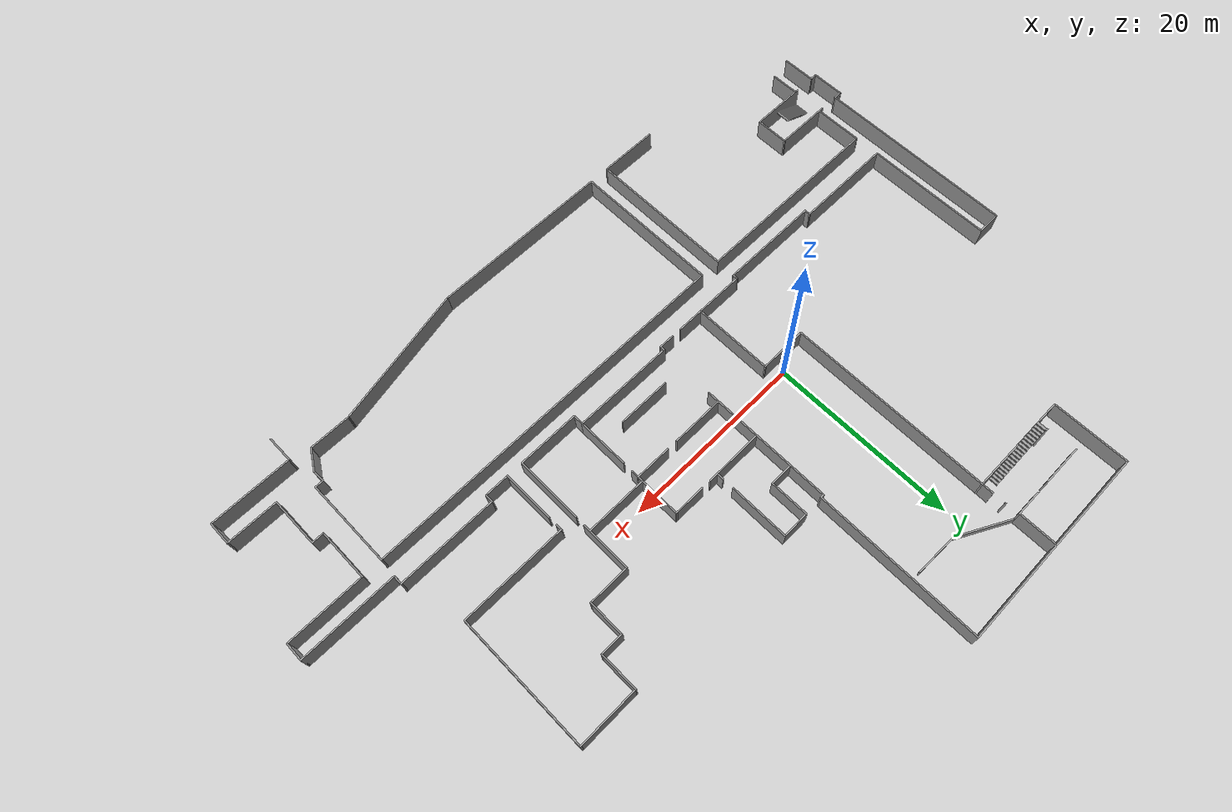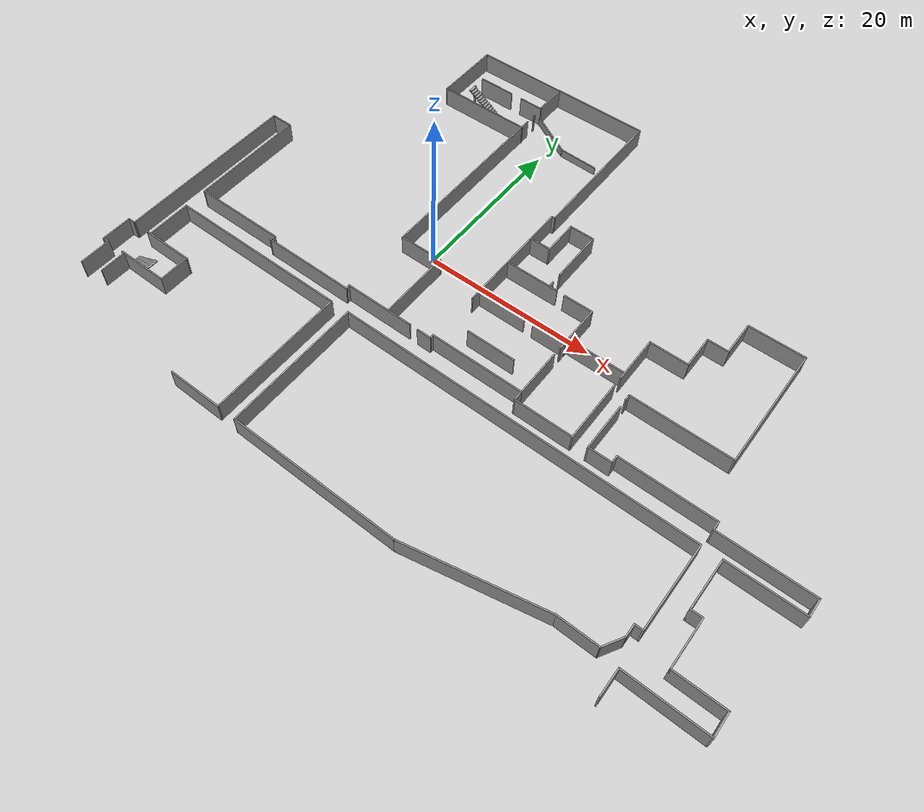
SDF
<?xml version='1.0'?>
<sdf version='1.6'>
  <model name='uia_section'>
    <pose frame=''>10.5615 0.198111 0 0 -0 0</pose>
    <link name='Stairs_1'>
      <visual name='Stairs_1_Visual_0'>
        <pose frame=''>-36.0937 -20.6482 0.058333 0 -0 1.5708</pose>
        <geometry>
          <box>
            <size>1.646 0.228733 0.116667</size>
          </box>
        </geometry>
        <material>
          <script>
            <uri>file://media/materials/scripts/gazebo.material</uri>
            <name>Gazebo/Grey</name>
          </script>
          <ambient>1 1 1 1</ambient>
        </material>
        <meta>
          <layer>0</layer>
        </meta>
      </visual>
      <collision name='Stairs_1_Collision_0'>
        <geometry>
          <box>
            <size>1.646 0.228733 0.116667</size>
          </box>
        </geometry>
        <pose frame=''>-36.0937 -20.6482 0.058333 0 -0 1.5708</pose>
      </collision>
      <visual name='Stairs_1_Visual_1'>
        <pose frame=''>-35.865 -20.6482 0.175 0 -0 1.5708</pose>
        <geometry>
          <box>
            <size>1.646 0.228733 0.116667</size>
          </box>
        </geometry>
        <material>
          <script>
            <uri>file://media/materials/scripts/gazebo.material</uri>
            <name>Gazebo/Grey</name>
          </script>
          <ambient>1 1 1 1</ambient>
        </material>
        <meta>
          <layer>0</layer>
        </meta>
      </visual>
      <collision name='Stairs_1_Collision_1'>
        <geometry>
          <box>
            <size>1.646 0.228733 0.116667</size>
          </box>
        </geometry>
        <pose frame=''>-35.865 -20.6482 0.175 0 -0 1.5708</pose>
      </collision>
      <visual name='Stairs_1_Visual_2'>
        <pose frame=''>-35.6363 -20.6482 0.291667 0 -0 1.5708</pose>
        <geometry>
          <box>
            <size>1.646 0.228733 0.116667</size>
          </box>
        </geometry>
        <material>
          <script>
            <uri>file://media/materials/scripts/gazebo.material</uri>
            <name>Gazebo/Grey</name>
          </script>
          <ambient>1 1 1 1</ambient>
        </material>
        <meta>
          <layer>0</layer>
        </meta>
      </visual>
      <collision name='Stairs_1_Collision_2'>
        <geometry>
          <box>
            <size>1.646 0.228733 0.116667</size>
          </box>
        </geometry>
        <pose frame=''>-35.6363 -20.6482 0.291667 0 -0 1.5708</pose>
      </collision>
      <visual name='Stairs_1_Visual_3'>
        <pose frame=''>-35.4075 -20.6482 0.408333 0 -0 1.5708</pose>
        <geometry>
          <box>
            <size>1.646 0.228733 0.116667</size>
          </box>
        </geometry>
        <material>
          <script>
            <uri>file://media/materials/scripts/gazebo.material</uri>
            <name>Gazebo/Grey</name>
          </script>
          <ambient>1 1 1 1</ambient>
        </material>
        <meta>
          <layer>0</layer>
        </meta>
      </visual>
      <collision name='Stairs_1_Collision_3'>
        <geometry>
          <box>
            <size>1.646 0.228733 0.116667</size>
          </box>
        </geometry>
        <pose frame=''>-35.4075 -20.6482 0.408333 0 -0 1.5708</pose>
      </collision>
      <visual name='Stairs_1_Visual_4'>
        <pose frame=''>-35.1788 -20.6482 0.525 0 -0 1.5708</pose>
        <geometry>
          <box>
            <size>1.646 0.228733 0.116667</size>
          </box>
        </geometry>
        <material>
          <script>
            <uri>file://media/materials/scripts/gazebo.material</uri>
            <name>Gazebo/Grey</name>
          </script>
          <ambient>1 1 1 1</ambient>
        </material>
        <meta>
          <layer>0</layer>
        </meta>
      </visual>
      <collision name='Stairs_1_Collision_4'>
        <geometry>
          <box>
            <size>1.646 0.228733 0.116667</size>
          </box>
        </geometry>
        <pose frame=''>-35.1788 -20.6482 0.525 0 -0 1.5708</pose>
      </collision>
      <visual name='Stairs_1_Visual_5'>
        <pose frame=''>-34.9501 -20.6482 0.641667 0 -0 1.5708</pose>
        <geometry>
          <box>
            <size>1.646 0.228733 0.116667</size>
          </box>
        </geometry>
        <material>
          <script>
            <uri>file://media/materials/scripts/gazebo.material</uri>
            <name>Gazebo/Grey</name>
          </script>
          <ambient>1 1 1 1</ambient>
        </material>
        <meta>
          <layer>0</layer>
        </meta>
      </visual>
      <collision name='Stairs_1_Collision_5'>
        <geometry>
          <box>
            <size>1.646 0.228733 0.116667</size>
          </box>
        </geometry>
        <pose frame=''>-34.9501 -20.6482 0.641667 0 -0 1.5708</pose>
      </collision>
      <visual name='Stairs_1_Visual_6'>
        <pose frame=''>-34.7213 -20.6482 0.758333 0 -0 1.5708</pose>
        <geometry>
          <box>
            <size>1.646 0.228733 0.116667</size>
          </box>
        </geometry>
        <material>
          <script>
            <uri>file://media/materials/scripts/gazebo.material</uri>
            <name>Gazebo/Grey</name>
          </script>
          <ambient>1 1 1 1</ambient>
        </material>
        <meta>
          <layer>0</layer>
        </meta>
      </visual>
      <collision name='Stairs_1_Collision_6'>
        <geometry>
          <box>
            <size>1.646 0.228733 0.116667</size>
          </box>
        </geometry>
        <pose frame=''>-34.7213 -20.6482 0.758333 0 -0 1.5708</pose>
      </collision>
      <visual name='Stairs_1_Visual_7'>
        <pose frame=''>-34.4926 -20.6482 0.875 0 -0 1.5708</pose>
        <geometry>
          <box>
            <size>1.646 0.228733 0.116667</size>
          </box>
        </geometry>
        <material>
          <script>
            <uri>file://media/materials/scripts/gazebo.material</uri>
            <name>Gazebo/Grey</name>
          </script>
          <ambient>1 1 1 1</ambient>
        </material>
        <meta>
          <layer>0</layer>
        </meta>
      </visual>
      <collision name='Stairs_1_Collision_7'>
        <geometry>
          <box>
            <size>1.646 0.228733 0.116667</size>
          </box>
        </geometry>
        <pose frame=''>-34.4926 -20.6482 0.875 0 -0 1.5708</pose>
      </collision>
      <visual name='Stairs_1_Visual_8'>
        <pose frame=''>-34.2639 -20.6482 0.991667 0 -0 1.5708</pose>
        <geometry>
          <box>
            <size>1.646 0.228733 0.116667</size>
          </box>
        </geometry>
        <material>
          <script>
            <uri>file://media/materials/scripts/gazebo.material</uri>
            <name>Gazebo/Grey</name>
          </script>
          <ambient>1 1 1 1</ambient>
        </material>
        <meta>
          <layer>0</layer>
        </meta>
      </visual>
      <collision name='Stairs_1_Collision_8'>
        <geometry>
          <box>
            <size>1.646 0.228733 0.116667</size>
          </box>
        </geometry>
        <pose frame=''>-34.2639 -20.6482 0.991667 0 -0 1.5708</pose>
      </collision>
      <visual name='Stairs_1_Visual_9'>
        <pose frame=''>-34.0351 -20.6482 1.10833 0 -0 1.5708</pose>
        <geometry>
          <box>
            <size>1.646 0.228733 0.116667</size>
          </box>
        </geometry>
        <material>
          <script>
            <uri>file://media/materials/scripts/gazebo.material</uri>
            <name>Gazebo/Grey</name>
          </script>
          <ambient>1 1 1 1</ambient>
        </material>
        <meta>
          <layer>0</layer>
        </meta>
      </visual>
      <collision name='Stairs_1_Collision_9'>
        <geometry>
          <box>
            <size>1.646 0.228733 0.116667</size>
          </box>
        </geometry>
        <pose frame=''>-34.0351 -20.6482 1.10833 0 -0 1.5708</pose>
      </collision>
      <visual name='Stairs_1_Visual_10'>
        <pose frame=''>-33.8064 -20.6482 1.225 0 -0 1.5708</pose>
        <geometry>
          <box>
            <size>1.646 0.228733 0.116667</size>
          </box>
        </geometry>
        <material>
          <script>
            <uri>file://media/materials/scripts/gazebo.material</uri>
            <name>Gazebo/Grey</name>
          </script>
          <ambient>1 1 1 1</ambient>
        </material>
        <meta>
          <layer>0</layer>
        </meta>
      </visual>
      <collision name='Stairs_1_Collision_10'>
        <geometry>
          <box>
            <size>1.646 0.228733 0.116667</size>
          </box>
        </geometry>
        <pose frame=''>-33.8064 -20.6482 1.225 0 -0 1.5708</pose>
      </collision>
      <visual name='Stairs_1_Visual_11'>
        <pose frame=''>-33.5777 -20.6482 1.34167 0 -0 1.5708</pose>
        <geometry>
          <box>
            <size>1.646 0.228733 0.116667</size>
          </box>
        </geometry>
        <material>
          <script>
            <uri>file://media/materials/scripts/gazebo.material</uri>
            <name>Gazebo/Grey</name>
          </script>
          <ambient>1 1 1 1</ambient>
        </material>
        <meta>
          <layer>0</layer>
        </meta>
      </visual>
      <collision name='Stairs_1_Collision_11'>
        <geometry>
          <box>
            <size>1.646 0.228733 0.116667</size>
          </box>
        </geometry>
        <pose frame=''>-33.5777 -20.6482 1.34167 0 -0 1.5708</pose>
      </collision>
      <visual name='Stairs_1_Visual_12'>
        <pose frame=''>-33.3489 -20.6482 1.45833 0 -0 1.5708</pose>
        <geometry>
          <box>
            <size>1.646 0.228733 0.116667</size>
          </box>
        </geometry>
        <material>
          <script>
            <uri>file://media/materials/scripts/gazebo.material</uri>
            <name>Gazebo/Grey</name>
          </script>
          <ambient>1 1 1 1</ambient>
        </material>
        <meta>
          <layer>0</layer>
        </meta>
      </visual>
      <collision name='Stairs_1_Collision_12'>
        <geometry>
          <box>
            <size>1.646 0.228733 0.116667</size>
          </box>
        </geometry>
        <pose frame=''>-33.3489 -20.6482 1.45833 0 -0 1.5708</pose>
      </collision>
      <visual name='Stairs_1_Visual_13'>
        <pose frame=''>-33.1202 -20.6482 1.575 0 -0 1.5708</pose>
        <geometry>
          <box>
            <size>1.646 0.228733 0.116667</size>
          </box>
        </geometry>
        <material>
          <script>
            <uri>file://media/materials/scripts/gazebo.material</uri>
            <name>Gazebo/Grey</name>
          </script>
          <ambient>1 1 1 1</ambient>
        </material>
        <meta>
          <layer>0</layer>
        </meta>
      </visual>
      <collision name='Stairs_1_Collision_13'>
        <geometry>
          <box>
            <size>1.646 0.228733 0.116667</size>
          </box>
        </geometry>
        <pose frame=''>-33.1202 -20.6482 1.575 0 -0 1.5708</pose>
      </collision>
      <visual name='Stairs_1_Visual_14'>
        <pose frame=''>-32.8915 -20.6482 1.69167 0 -0 1.5708</pose>
        <geometry>
          <box>
            <size>1.646 0.228733 0.116667</size>
          </box>
        </geometry>
        <material>
          <script>
            <uri>file://media/materials/scripts/gazebo.material</uri>
            <name>Gazebo/Grey</name>
          </script>
          <ambient>1 1 1 1</ambient>
        </material>
        <meta>
          <layer>0</layer>
        </meta>
      </visual>
      <collision name='Stairs_1_Collision_14'>
        <geometry>
          <box>
            <size>1.646 0.228733 0.116667</size>
          </box>
        </geometry>
        <pose frame=''>-32.8915 -20.6482 1.69167 0 -0 1.5708</pose>
      </collision>
    </link>
    <link name='Stairs_4'>
      <visual name='Stairs_4_Visual_0'>
        <pose frame=''>-16.0582 21.3116 0.1 0 0 -1.5708</pose>
        <geometry>
          <box>
            <size>1 0.292 0.2</size>
          </box>
        </geometry>
        <material>
          <script>
            <uri>file://media/materials/scripts/gazebo.material</uri>
            <name>Gazebo/Grey</name>
          </script>
          <ambient>1 1 1 1</ambient>
        </material>
        <meta>
          <layer>0</layer>
        </meta>
      </visual>
      <collision name='Stairs_4_Collision_0'>
        <geometry>
          <box>
            <size>1 0.292 0.2</size>
          </box>
        </geometry>
        <pose frame=''>-16.0582 21.3116 0.1 0 0 -1.5708</pose>
      </collision>
      <visual name='Stairs_4_Visual_1'>
        <pose frame=''>-16.3502 21.3116 0.3 0 0 -1.5708</pose>
        <geometry>
          <box>
            <size>1 0.292 0.2</size>
          </box>
        </geometry>
        <material>
          <script>
            <uri>file://media/materials/scripts/gazebo.material</uri>
            <name>Gazebo/Grey</name>
          </script>
          <ambient>1 1 1 1</ambient>
        </material>
        <meta>
          <layer>0</layer>
        </meta>
      </visual>
      <collision name='Stairs_4_Collision_1'>
        <geometry>
          <box>
            <size>1 0.292 0.2</size>
          </box>
        </geometry>
        <pose frame=''>-16.3502 21.3116 0.3 0 0 -1.5708</pose>
      </collision>
      <visual name='Stairs_4_Visual_2'>
        <pose frame=''>-16.6422 21.3116 0.5 0 0 -1.5708</pose>
        <geometry>
          <box>
            <size>1 0.292 0.2</size>
          </box>
        </geometry>
        <material>
          <script>
            <uri>file://media/materials/scripts/gazebo.material</uri>
            <name>Gazebo/Grey</name>
          </script>
          <ambient>1 1 1 1</ambient>
        </material>
        <meta>
          <layer>0</layer>
        </meta>
      </visual>
      <collision name='Stairs_4_Collision_2'>
        <geometry>
          <box>
            <size>1 0.292 0.2</size>
          </box>
        </geometry>
        <pose frame=''>-16.6422 21.3116 0.5 0 0 -1.5708</pose>
      </collision>
      <visual name='Stairs_4_Visual_3'>
        <pose frame=''>-16.9342 21.3116 0.7 0 0 -1.5708</pose>
        <geometry>
          <box>
            <size>1 0.292 0.2</size>
          </box>
        </geometry>
        <material>
          <script>
            <uri>file://media/materials/scripts/gazebo.material</uri>
            <name>Gazebo/Grey</name>
          </script>
          <ambient>1 1 1 1</ambient>
        </material>
        <meta>
          <layer>0</layer>
        </meta>
      </visual>
      <collision name='Stairs_4_Collision_3'>
        <geometry>
          <box>
            <size>1 0.292 0.2</size>
          </box>
        </geometry>
        <pose frame=''>-16.9342 21.3116 0.7 0 0 -1.5708</pose>
      </collision>
      <visual name='Stairs_4_Visual_4'>
        <pose frame=''>-17.2262 21.3116 0.9 0 0 -1.5708</pose>
        <geometry>
          <box>
            <size>1 0.292 0.2</size>
          </box>
        </geometry>
        <material>
          <script>
            <uri>file://media/materials/scripts/gazebo.material</uri>
            <name>Gazebo/Grey</name>
          </script>
          <ambient>1 1 1 1</ambient>
        </material>
        <meta>
          <layer>0</layer>
        </meta>
      </visual>
      <collision name='Stairs_4_Collision_4'>
        <geometry>
          <box>
            <size>1 0.292 0.2</size>
          </box>
        </geometry>
        <pose frame=''>-17.2262 21.3116 0.9 0 0 -1.5708</pose>
      </collision>
      <visual name='Stairs_4_Visual_5'>
        <pose frame=''>-17.5182 21.3116 1.1 0 0 -1.5708</pose>
        <geometry>
          <box>
            <size>1 0.292 0.2</size>
          </box>
        </geometry>
        <material>
          <script>
            <uri>file://media/materials/scripts/gazebo.material</uri>
            <name>Gazebo/Grey</name>
          </script>
          <ambient>1 1 1 1</ambient>
        </material>
        <meta>
          <layer>0</layer>
        </meta>
      </visual>
      <collision name='Stairs_4_Collision_5'>
        <geometry>
          <box>
            <size>1 0.292 0.2</size>
          </box>
        </geometry>
        <pose frame=''>-17.5182 21.3116 1.1 0 0 -1.5708</pose>
      </collision>
      <visual name='Stairs_4_Visual_6'>
        <pose frame=''>-17.8102 21.3116 1.3 0 0 -1.5708</pose>
        <geometry>
          <box>
            <size>1 0.292 0.2</size>
          </box>
        </geometry>
        <material>
          <script>
            <uri>file://media/materials/scripts/gazebo.material</uri>
            <name>Gazebo/Grey</name>
          </script>
          <ambient>1 1 1 1</ambient>
        </material>
        <meta>
          <layer>0</layer>
        </meta>
      </visual>
      <collision name='Stairs_4_Collision_6'>
        <geometry>
          <box>
            <size>1 0.292 0.2</size>
          </box>
        </geometry>
        <pose frame=''>-17.8102 21.3116 1.3 0 0 -1.5708</pose>
      </collision>
      <visual name='Stairs_4_Visual_7'>
        <pose frame=''>-18.1022 21.3116 1.5 0 0 -1.5708</pose>
        <geometry>
          <box>
            <size>1 0.292 0.2</size>
          </box>
        </geometry>
        <material>
          <script>
            <uri>file://media/materials/scripts/gazebo.material</uri>
            <name>Gazebo/Grey</name>
          </script>
          <ambient>1 1 1 1</ambient>
        </material>
        <meta>
          <layer>0</layer>
        </meta>
      </visual>
      <collision name='Stairs_4_Collision_7'>
        <geometry>
          <box>
            <size>1 0.292 0.2</size>
          </box>
        </geometry>
        <pose frame=''>-18.1022 21.3116 1.5 0 0 -1.5708</pose>
      </collision>
      <visual name='Stairs_4_Visual_8'>
        <pose frame=''>-18.3942 21.3116 1.7 0 0 -1.5708</pose>
        <geometry>
          <box>
            <size>1 0.292 0.2</size>
          </box>
        </geometry>
        <material>
          <script>
            <uri>file://media/materials/scripts/gazebo.material</uri>
            <name>Gazebo/Grey</name>
          </script>
          <ambient>1 1 1 1</ambient>
        </material>
        <meta>
          <layer>0</layer>
        </meta>
      </visual>
      <collision name='Stairs_4_Collision_8'>
        <geometry>
          <box>
            <size>1 0.292 0.2</size>
          </box>
        </geometry>
        <pose frame=''>-18.3942 21.3116 1.7 0 0 -1.5708</pose>
      </collision>
      <visual name='Stairs_4_Visual_9'>
        <pose frame=''>-18.6862 21.3116 1.9 0 0 -1.5708</pose>
        <geometry>
          <box>
            <size>1 0.292 0.2</size>
          </box>
        </geometry>
        <material>
          <script>
            <uri>file://media/materials/scripts/gazebo.material</uri>
            <name>Gazebo/Grey</name>
          </script>
          <ambient>1 1 1 1</ambient>
        </material>
        <meta>
          <layer>0</layer>
        </meta>
      </visual>
      <collision name='Stairs_4_Collision_9'>
        <geometry>
          <box>
            <size>1 0.292 0.2</size>
          </box>
        </geometry>
        <pose frame=''>-18.6862 21.3116 1.9 0 0 -1.5708</pose>
      </collision>
      <visual name='Stairs_4_Visual_10'>
        <pose frame=''>-18.9782 21.3116 2.1 0 0 -1.5708</pose>
        <geometry>
          <box>
            <size>1 0.292 0.2</size>
          </box>
        </geometry>
        <material>
          <script>
            <uri>file://media/materials/scripts/gazebo.material</uri>
            <name>Gazebo/Grey</name>
          </script>
          <ambient>1 1 1 1</ambient>
        </material>
        <meta>
          <layer>0</layer>
        </meta>
      </visual>
      <collision name='Stairs_4_Collision_10'>
        <geometry>
          <box>
            <size>1 0.292 0.2</size>
          </box>
        </geometry>
        <pose frame=''>-18.9782 21.3116 2.1 0 0 -1.5708</pose>
      </collision>
      <visual name='Stairs_4_Visual_11'>
        <pose frame=''>-19.2702 21.3116 2.3 0 0 -1.5708</pose>
        <geometry>
          <box>
            <size>1 0.292 0.2</size>
          </box>
        </geometry>
        <material>
          <script>
            <uri>file://media/materials/scripts/gazebo.material</uri>
            <name>Gazebo/Grey</name>
          </script>
          <ambient>1 1 1 1</ambient>
        </material>
        <meta>
          <layer>0</layer>
        </meta>
      </visual>
      <collision name='Stairs_4_Collision_11'>
        <geometry>
          <box>
            <size>1 0.292 0.2</size>
          </box>
        </geometry>
        <pose frame=''>-19.2702 21.3116 2.3 0 0 -1.5708</pose>
      </collision>
      <visual name='Stairs_4_Visual_12'>
        <pose frame=''>-19.5622 21.3116 2.5 0 0 -1.5708</pose>
        <geometry>
          <box>
            <size>1 0.292 0.2</size>
          </box>
        </geometry>
        <material>
          <script>
            <uri>file://media/materials/scripts/gazebo.material</uri>
            <name>Gazebo/Grey</name>
          </script>
          <ambient>1 1 1 1</ambient>
        </material>
        <meta>
          <layer>0</layer>
        </meta>
      </visual>
      <collision name='Stairs_4_Collision_12'>
        <geometry>
          <box>
            <size>1 0.292 0.2</size>
          </box>
        </geometry>
        <pose frame=''>-19.5622 21.3116 2.5 0 0 -1.5708</pose>
      </collision>
      <visual name='Stairs_4_Visual_13'>
        <pose frame=''>-19.8542 21.3116 2.7 0 0 -1.5708</pose>
        <geometry>
          <box>
            <size>1 0.292 0.2</size>
          </box>
        </geometry>
        <material>
          <script>
            <uri>file://media/materials/scripts/gazebo.material</uri>
            <name>Gazebo/Grey</name>
          </script>
          <ambient>1 1 1 1</ambient>
        </material>
        <meta>
          <layer>0</layer>
        </meta>
      </visual>
      <collision name='Stairs_4_Collision_13'>
        <geometry>
          <box>
            <size>1 0.292 0.2</size>
          </box>
        </geometry>
        <pose frame=''>-19.8542 21.3116 2.7 0 0 -1.5708</pose>
      </collision>
      <visual name='Stairs_4_Visual_14'>
        <pose frame=''>-20.1462 21.3116 2.9 0 0 -1.5708</pose>
        <geometry>
          <box>
            <size>1 0.292 0.2</size>
          </box>
        </geometry>
        <material>
          <script>
            <uri>file://media/materials/scripts/gazebo.material</uri>
            <name>Gazebo/Grey</name>
          </script>
          <ambient>1 1 1 1</ambient>
        </material>
        <meta>
          <layer>0</layer>
        </meta>
      </visual>
      <collision name='Stairs_4_Collision_14'>
        <geometry>
          <box>
            <size>1 0.292 0.2</size>
          </box>
        </geometry>
        <pose frame=''>-20.1462 21.3116 2.9 0 0 -1.5708</pose>
      </collision>
      <visual name='Stairs_4_Visual_15'>
        <pose frame=''>-20.4382 21.3116 3.1 0 0 -1.5708</pose>
        <geometry>
          <box>
            <size>1 0.292 0.2</size>
          </box>
        </geometry>
        <material>
          <script>
            <uri>file://media/materials/scripts/gazebo.material</uri>
            <name>Gazebo/Grey</name>
          </script>
          <ambient>1 1 1 1</ambient>
        </material>
        <meta>
          <layer>0</layer>
        </meta>
      </visual>
      <collision name='Stairs_4_Collision_15'>
        <geometry>
          <box>
            <size>1 0.292 0.2</size>
          </box>
        </geometry>
        <pose frame=''>-20.4382 21.3116 3.1 0 0 -1.5708</pose>
      </collision>
      <visual name='Stairs_4_Visual_16'>
        <pose frame=''>-20.7302 21.3116 3.3 0 0 -1.5708</pose>
        <geometry>
          <box>
            <size>1 0.292 0.2</size>
          </box>
        </geometry>
        <material>
          <script>
            <uri>file://media/materials/scripts/gazebo.material</uri>
            <name>Gazebo/Grey</name>
          </script>
          <ambient>1 1 1 1</ambient>
        </material>
        <meta>
          <layer>0</layer>
        </meta>
      </visual>
      <collision name='Stairs_4_Collision_16'>
        <geometry>
          <box>
            <size>1 0.292 0.2</size>
          </box>
        </geometry>
        <pose frame=''>-20.7302 21.3116 3.3 0 0 -1.5708</pose>
      </collision>
      <visual name='Stairs_4_Visual_17'>
        <pose frame=''>-21.0222 21.3116 3.5 0 0 -1.5708</pose>
        <geometry>
          <box>
            <size>1 0.292 0.2</size>
          </box>
        </geometry>
        <material>
          <script>
            <uri>file://media/materials/scripts/gazebo.material</uri>
            <name>Gazebo/Grey</name>
          </script>
          <ambient>1 1 1 1</ambient>
        </material>
        <meta>
          <layer>0</layer>
        </meta>
      </visual>
      <collision name='Stairs_4_Collision_17'>
        <geometry>
          <box>
            <size>1 0.292 0.2</size>
          </box>
        </geometry>
        <pose frame=''>-21.0222 21.3116 3.5 0 0 -1.5708</pose>
      </collision>
      <visual name='Stairs_4_Visual_18'>
        <pose frame=''>-21.3142 21.3116 3.7 0 0 -1.5708</pose>
        <geometry>
          <box>
            <size>1 0.292 0.2</size>
          </box>
        </geometry>
        <material>
          <script>
            <uri>file://media/materials/scripts/gazebo.material</uri>
            <name>Gazebo/Grey</name>
          </script>
          <ambient>1 1 1 1</ambient>
        </material>
        <meta>
          <layer>0</layer>
        </meta>
      </visual>
      <collision name='Stairs_4_Collision_18'>
        <geometry>
          <box>
            <size>1 0.292 0.2</size>
          </box>
        </geometry>
        <pose frame=''>-21.3142 21.3116 3.7 0 0 -1.5708</pose>
      </collision>
      <visual name='Stairs_4_Visual_19'>
        <pose frame=''>-21.6062 21.3116 3.9 0 0 -1.5708</pose>
        <geometry>
          <box>
            <size>1 0.292 0.2</size>
          </box>
        </geometry>
        <material>
          <script>
            <uri>file://media/materials/scripts/gazebo.material</uri>
            <name>Gazebo/Grey</name>
          </script>
          <ambient>1 1 1 1</ambient>
        </material>
        <meta>
          <layer>0</layer>
        </meta>
      </visual>
      <collision name='Stairs_4_Collision_19'>
        <geometry>
          <box>
            <size>1 0.292 0.2</size>
          </box>
        </geometry>
        <pose frame=''>-21.6062 21.3116 3.9 0 0 -1.5708</pose>
      </collision>
    </link>
    <link name='Wall_0'>
      <collision name='Wall_0_Collision'>
        <geometry>
          <box>
            <size>7.45 0.15 2.5</size>
          </box>
        </geometry>
        <pose frame=''>0 0 1.25 0 -0 0</pose>
      </collision>
      <visual name='Wall_0_Visual'>
        <pose frame=''>0 0 1.25 0 -0 0</pose>
        <geometry>
          <box>
            <size>7.45 0.15 2.5</size>
          </box>
        </geometry>
        <material>
          <script>
            <uri>file://media/materials/scripts/gazebo.material</uri>
            <name>Gazebo/Grey</name>
          </script>
          <ambient>1 1 1 1</ambient>
        </material>
        <meta>
          <layer>0</layer>
        </meta>
      </visual>
      <pose frame=''>14.1915 -6.99111 0 0 -0 1.5708</pose>
    </link>
    <link name='Wall_10'>
      <collision name='Wall_10_Collision'>
        <geometry>
          <box>
            <size>5.6 0.15 2.5</size>
          </box>
        </geometry>
        <pose frame=''>0 0 1.25 0 -0 0</pose>
      </collision>
      <visual name='Wall_10_Visual'>
        <pose frame=''>0 0 1.25 0 -0 0</pose>
        <geometry>
          <box>
            <size>5.6 0.15 2.5</size>
          </box>
        </geometry>
        <material>
          <script>
            <uri>file://media/materials/scripts/gazebo.material</uri>
            <name>Gazebo/Grey</name>
          </script>
          <ambient>1 1 1 1</ambient>
        </material>
        <meta>
          <layer>0</layer>
        </meta>
      </visual>
      <pose frame=''>14.2238 0.523029 0 0 -0 -1.5708</pose>
    </link>
    <link name='Wall_100'>
      <collision name='Wall_100_Collision'>
        <geometry>
          <box>
            <size>2.94746 0.15 2.5</size>
          </box>
        </geometry>
        <pose frame=''>0 0 1.25 0 -0 0</pose>
      </collision>
      <visual name='Wall_100_Visual'>
        <pose frame=''>0 0 1.25 0 -0 0</pose>
        <geometry>
          <box>
            <size>2.94746 0.15 2.5</size>
          </box>
        </geometry>
        <material>
          <script>
            <uri>file://media/materials/scripts/gazebo.material</uri>
            <name>Gazebo/Grey</name>
          </script>
          <ambient>1 1 1 1</ambient>
        </material>
        <meta>
          <layer>0</layer>
        </meta>
      </visual>
      <pose frame=''>-15.482 24.9228 0 0 -0 -3.14153</pose>
    </link>
    <link name='Wall_102'>
      <collision name='Wall_102_Collision'>
        <geometry>
          <box>
            <size>4.5 0.15 2.5</size>
          </box>
        </geometry>
        <pose frame=''>0 0 1.25 0 -0 0</pose>
      </collision>
      <visual name='Wall_102_Visual'>
        <pose frame=''>0 0 1.25 0 -0 0</pose>
        <geometry>
          <box>
            <size>4.5 0.15 2.5</size>
          </box>
        </geometry>
        <material>
          <script>
            <uri>file://media/materials/scripts/gazebo.material</uri>
            <name>Gazebo/Grey</name>
          </script>
          <ambient>1 1 1 1</ambient>
        </material>
        <meta>
          <layer>0</layer>
        </meta>
      </visual>
      <pose frame=''>-20.5803 24.9407 0 0 -0 3.14159</pose>
    </link>
    <link name='Wall_104'>
      <collision name='Wall_104_Collision'>
        <geometry>
          <box>
            <size>3.75 0.15 2.5</size>
          </box>
        </geometry>
        <pose frame=''>0 0 1.25 0 -0 0</pose>
      </collision>
      <visual name='Wall_104_Visual'>
        <pose frame=''>0 0 1.25 0 -0 0</pose>
        <geometry>
          <box>
            <size>3.75 0.15 2.5</size>
          </box>
        </geometry>
        <material>
          <script>
            <uri>file://media/materials/scripts/gazebo.material</uri>
            <name>Gazebo/Grey</name>
          </script>
          <ambient>1 1 1 1</ambient>
        </material>
        <meta>
          <layer>0</layer>
        </meta>
      </visual>
      <pose frame=''>-30.0635 -19.7841 0 0 -0 1.5708</pose>
    </link>
    <link name='Wall_12'>
      <collision name='Wall_12_Collision'>
        <geometry>
          <box>
            <size>0.75 0.15 2.5</size>
          </box>
        </geometry>
        <pose frame=''>0 0 1.25 0 -0 0</pose>
      </collision>
      <visual name='Wall_12_Visual'>
        <pose frame=''>0 0 1.25 0 -0 0</pose>
        <geometry>
          <box>
            <size>0.75 0.15 2.5</size>
          </box>
        </geometry>
        <material>
          <script>
            <uri>file://media/materials/scripts/gazebo.material</uri>
            <name>Gazebo/Grey</name>
          </script>
          <ambient>1 1 1 1</ambient>
        </material>
        <meta>
          <layer>0</layer>
        </meta>
      </visual>
      <pose frame=''>15.9238 -3.70197 0 0 -0 -1.5708</pose>
    </link>
    <link name='Wall_15'>
      <collision name='Wall_15_Collision'>
        <geometry>
          <box>
            <size>5.762 0.15 2.5</size>
          </box>
        </geometry>
        <pose frame=''>0 0 1.25 0 -0 0</pose>
      </collision>
      <visual name='Wall_15_Visual'>
        <pose frame=''>0 0 1.25 0 -0 0</pose>
        <geometry>
          <box>
            <size>5.762 0.15 2.5</size>
          </box>
        </geometry>
        <material>
          <script>
            <uri>file://media/materials/scripts/gazebo.material</uri>
            <name>Gazebo/Grey</name>
          </script>
          <ambient>1 1 1 1</ambient>
        </material>
        <meta>
          <layer>0</layer>
        </meta>
      </visual>
      <pose frame=''>15.9415 -7.83511 0 0 -0 -1.5708</pose>
    </link>
    <link name='Wall_161'>
      <collision name='Wall_161_Collision'>
        <geometry>
          <box>
            <size>11.553 0.15 2.5</size>
          </box>
        </geometry>
        <pose frame=''>0 0 1.25 0 -0 0</pose>
      </collision>
      <visual name='Wall_161_Visual'>
        <pose frame=''>0 0 1.25 0 -0 0</pose>
        <geometry>
          <box>
            <size>11.553 0.15 2.5</size>
          </box>
        </geometry>
        <material>
          <script>
            <uri>file://media/materials/scripts/gazebo.material</uri>
            <name>Gazebo/Grey</name>
          </script>
          <ambient>1 1 1 1</ambient>
        </material>
        <meta>
          <layer>0</layer>
        </meta>
      </visual>
      <pose frame=''>-8.382 29.0229 0 0 -0 0</pose>
    </link>
    <link name='Wall_162'>
      <collision name='Wall_162_Collision'>
        <geometry>
          <box>
            <size>18 0.15 2.5</size>
          </box>
        </geometry>
        <pose frame=''>0 0 1.25 0 -0 0</pose>
      </collision>
      <visual name='Wall_162_Visual'>
        <pose frame=''>0 0 1.25 0 -0 0</pose>
        <geometry>
          <box>
            <size>18 0.15 2.5</size>
          </box>
        </geometry>
        <material>
          <script>
            <uri>file://media/materials/scripts/gazebo.material</uri>
            <name>Gazebo/Grey</name>
          </script>
          <ambient>1 1 1 1</ambient>
        </material>
        <meta>
          <layer>0</layer>
        </meta>
      </visual>
      <pose frame=''>-2.6805 20.0979 0 0 -0 -1.5708</pose>
    </link>
    <link name='Wall_163'>
      <collision name='Wall_163_Collision'>
        <geometry>
          <box>
            <size>0.488 0.15 2.5</size>
          </box>
        </geometry>
        <pose frame=''>0 0 1.25 0 -0 0</pose>
      </collision>
      <visual name='Wall_163_Visual'>
        <pose frame=''>0 0 1.25 0 -0 0</pose>
        <geometry>
          <box>
            <size>0.488 0.15 2.5</size>
          </box>
        </geometry>
        <material>
          <script>
            <uri>file://media/materials/scripts/gazebo.material</uri>
            <name>Gazebo/Grey</name>
          </script>
          <ambient>1 1 1 1</ambient>
        </material>
        <meta>
          <layer>0</layer>
        </meta>
      </visual>
      <pose frame=''>-2.8495 11.1729 0 0 -0 3.14159</pose>
    </link>
    <link name='Wall_164'>
      <collision name='Wall_164_Collision'>
        <geometry>
          <box>
            <size>14.5908 0.15 2.5</size>
          </box>
        </geometry>
        <pose frame=''>0 0 1.25 0 -0 0</pose>
      </collision>
      <visual name='Wall_164_Visual'>
        <pose frame=''>0 0 1.25 0 -0 0</pose>
        <geometry>
          <box>
            <size>14.5908 0.15 2.5</size>
          </box>
        </geometry>
        <material>
          <script>
            <uri>file://media/materials/scripts/gazebo.material</uri>
            <name>Gazebo/Grey</name>
          </script>
          <ambient>1 1 1 1</ambient>
        </material>
        <meta>
          <layer>0</layer>
        </meta>
      </visual>
      <pose frame=''>-3.0185 3.95239 0 0 -0 -1.5708</pose>
    </link>
    <link name='Wall_166'>
      <collision name='Wall_166_Collision'>
        <geometry>
          <box>
            <size>5.75 0.15 2.5</size>
          </box>
        </geometry>
        <pose frame=''>0 0 1.25 0 -0 0</pose>
      </collision>
      <visual name='Wall_166_Visual'>
        <pose frame=''>0 0 1.25 0 -0 0</pose>
        <geometry>
          <box>
            <size>5.75 0.15 2.5</size>
          </box>
        </geometry>
        <material>
          <script>
            <uri>file://media/materials/scripts/gazebo.material</uri>
            <name>Gazebo/Grey</name>
          </script>
          <ambient>1 1 1 1</ambient>
        </material>
        <meta>
          <layer>0</layer>
        </meta>
      </visual>
      <pose frame=''>-0.211923 -2.01323 0 0 -0 0</pose>
    </link>
    <link name='Wall_168'>
      <collision name='Wall_168_Collision'>
        <geometry>
          <box>
            <size>4 0.15 2.5</size>
          </box>
        </geometry>
        <pose frame=''>0 0 1.25 0 -0 0</pose>
      </collision>
      <visual name='Wall_168_Visual'>
        <pose frame=''>0 0 1.25 0 -0 0</pose>
        <geometry>
          <box>
            <size>4 0.15 2.5</size>
          </box>
        </geometry>
        <material>
          <script>
            <uri>file://media/materials/scripts/gazebo.material</uri>
            <name>Gazebo/Grey</name>
          </script>
          <ambient>1 1 1 1</ambient>
        </material>
        <meta>
          <layer>0</layer>
        </meta>
      </visual>
      <pose frame=''>5.69496 -2.04392 0 0 -0 0</pose>
    </link>
    <link name='Wall_17'>
      <collision name='Wall_17_Collision'>
        <geometry>
          <box>
            <size>2.75 0.15 2.5</size>
          </box>
        </geometry>
        <pose frame=''>0 0 1.25 0 -0 0</pose>
      </collision>
      <visual name='Wall_17_Visual'>
        <pose frame=''>0 0 1.25 0 -0 0</pose>
        <geometry>
          <box>
            <size>2.75 0.15 2.5</size>
          </box>
        </geometry>
        <material>
          <script>
            <uri>file://media/materials/scripts/gazebo.material</uri>
            <name>Gazebo/Grey</name>
          </script>
          <ambient>1 1 1 1</ambient>
        </material>
        <meta>
          <layer>0</layer>
        </meta>
      </visual>
      <pose frame=''>17.2415 -10.6411 0 0 -0 0</pose>
    </link>
    <link name='Wall_170'>
      <collision name='Wall_170_Collision'>
        <geometry>
          <box>
            <size>1.5 0.15 2.5</size>
          </box>
        </geometry>
        <pose frame=''>0 0 1.25 0 -0 0</pose>
      </collision>
      <visual name='Wall_170_Visual'>
        <pose frame=''>0 0 1.25 0 -0 0</pose>
        <geometry>
          <box>
            <size>1.5 0.15 2.5</size>
          </box>
        </geometry>
        <material>
          <script>
            <uri>file://media/materials/scripts/gazebo.material</uri>
            <name>Gazebo/Grey</name>
          </script>
          <ambient>1 1 1 1</ambient>
        </material>
        <meta>
          <layer>0</layer>
        </meta>
      </visual>
      <pose frame=''>7.60587 -2.16678 0 0 -0 1.5708</pose>
    </link>
    <link name='Wall_171'>
      <collision name='Wall_171_Collision'>
        <geometry>
          <box>
            <size>6.75 0.15 2.5</size>
          </box>
        </geometry>
        <pose frame=''>0 0 1.25 0 -0 0</pose>
      </collision>
      <visual name='Wall_171_Visual'>
        <pose frame=''>0 0 1.25 0 -0 0</pose>
        <geometry>
          <box>
            <size>6.75 0.15 2.5</size>
          </box>
        </geometry>
        <material>
          <script>
            <uri>file://media/materials/scripts/gazebo.material</uri>
            <name>Gazebo/Grey</name>
          </script>
          <ambient>1 1 1 1</ambient>
        </material>
        <meta>
          <layer>0</layer>
        </meta>
      </visual>
      <pose frame=''>10.9059 -1.49178 0 0 -0 0</pose>
    </link>
    <link name='Wall_173'>
      <collision name='Wall_173_Collision'>
        <geometry>
          <box>
            <size>5.7 0.15 2.5</size>
          </box>
        </geometry>
        <pose frame=''>0 0 1.25 0 -0 0</pose>
      </collision>
      <visual name='Wall_173_Visual'>
        <pose frame=''>0 0 1.25 0 -0 0</pose>
        <geometry>
          <box>
            <size>5.7 0.15 2.5</size>
          </box>
        </geometry>
        <material>
          <script>
            <uri>file://media/materials/scripts/gazebo.material</uri>
            <name>Gazebo/Grey</name>
          </script>
          <ambient>1 1 1 1</ambient>
        </material>
        <meta>
          <layer>0</layer>
        </meta>
      </visual>
      <pose frame=''>7.5915 -6.76611 0 0 -0 1.5708</pose>
    </link>
    <link name='Wall_175'>
      <collision name='Wall_175_Collision'>
        <geometry>
          <box>
            <size>4.5 0.15 2.5</size>
          </box>
        </geometry>
        <pose frame=''>0 0 1.25 0 -0 0</pose>
      </collision>
      <visual name='Wall_175_Visual'>
        <pose frame=''>0 0 1.25 0 -0 0</pose>
        <geometry>
          <box>
            <size>4.5 0.15 2.5</size>
          </box>
        </geometry>
        <material>
          <script>
            <uri>file://media/materials/scripts/gazebo.material</uri>
            <name>Gazebo/Grey</name>
          </script>
          <ambient>1 1 1 1</ambient>
        </material>
        <meta>
          <layer>0</layer>
        </meta>
      </visual>
      <pose frame=''>7.60587 0.683215 0 0 -0 1.5708</pose>
    </link>
    <link name='Wall_176'>
      <collision name='Wall_176_Collision'>
        <geometry>
          <box>
            <size>3.5 0.15 2.5</size>
          </box>
        </geometry>
        <pose frame=''>0 0 1.25 0 -0 0</pose>
      </collision>
      <visual name='Wall_176_Visual'>
        <pose frame=''>0 0 1.25 0 -0 0</pose>
        <geometry>
          <box>
            <size>3.5 0.15 2.5</size>
          </box>
        </geometry>
        <material>
          <script>
            <uri>file://media/materials/scripts/gazebo.material</uri>
            <name>Gazebo/Grey</name>
          </script>
          <ambient>1 1 1 1</ambient>
        </material>
        <meta>
          <layer>0</layer>
        </meta>
      </visual>
      <pose frame=''>5.93087 2.85821 0 0 -0 3.14159</pose>
    </link>
    <link name='Wall_178'>
      <collision name='Wall_178_Collision'>
        <geometry>
          <box>
            <size>6.25 0.15 2.5</size>
          </box>
        </geometry>
        <pose frame=''>0 0 1.25 0 -0 0</pose>
      </collision>
      <visual name='Wall_178_Visual'>
        <pose frame=''>0 0 1.25 0 -0 0</pose>
        <geometry>
          <box>
            <size>6.25 0.15 2.5</size>
          </box>
        </geometry>
        <material>
          <script>
            <uri>file://media/materials/scripts/gazebo.material</uri>
            <name>Gazebo/Grey</name>
          </script>
          <ambient>1 1 1 1</ambient>
        </material>
        <meta>
          <layer>0</layer>
        </meta>
      </visual>
      <pose frame=''>0.166398 2.90441 0 0 -0 3.14159</pose>
    </link>
    <link name='Wall_18'>
      <collision name='Wall_18_Collision'>
        <geometry>
          <box>
            <size>1 0.15 2.5</size>
          </box>
        </geometry>
        <pose frame=''>0 0 1.25 0 -0 0</pose>
      </collision>
      <visual name='Wall_18_Visual'>
        <pose frame=''>0 0 1.25 0 -0 0</pose>
        <geometry>
          <box>
            <size>1 0.15 2.5</size>
          </box>
        </geometry>
        <material>
          <script>
            <uri>file://media/materials/scripts/gazebo.material</uri>
            <name>Gazebo/Grey</name>
          </script>
          <ambient>1 1 1 1</ambient>
        </material>
        <meta>
          <layer>0</layer>
        </meta>
      </visual>
      <pose frame=''>18.5415 -10.2161 0 0 -0 1.5708</pose>
    </link>
    <link name='Wall_180'>
      <collision name='Wall_180_Collision'>
        <geometry>
          <box>
            <size>2.5 0.15 2.5</size>
          </box>
        </geometry>
        <pose frame=''>0 0 1.25 0 -0 0</pose>
      </collision>
      <visual name='Wall_180_Visual'>
        <pose frame=''>0 0 1.25 0 -0 0</pose>
        <geometry>
          <box>
            <size>2.5 0.15 2.5</size>
          </box>
        </geometry>
        <material>
          <script>
            <uri>file://media/materials/scripts/gazebo.material</uri>
            <name>Gazebo/Grey</name>
          </script>
          <ambient>1 1 1 1</ambient>
        </material>
        <meta>
          <layer>0</layer>
        </meta>
      </visual>
      <pose frame=''>-1.74605 7.14725 0 0 -0 0</pose>
    </link>
    <link name='Wall_181'>
      <collision name='Wall_181_Collision'>
        <geometry>
          <box>
            <size>4.25 0.15 2.5</size>
          </box>
        </geometry>
        <pose frame=''>0 0 1.25 0 -0 0</pose>
      </collision>
      <visual name='Wall_181_Visual'>
        <pose frame=''>0 0 1.25 0 -0 0</pose>
        <geometry>
          <box>
            <size>4.25 0.15 2.5</size>
          </box>
        </geometry>
        <material>
          <script>
            <uri>file://media/materials/scripts/gazebo.material</uri>
            <name>Gazebo/Grey</name>
          </script>
          <ambient>1 1 1 1</ambient>
        </material>
        <meta>
          <layer>0</layer>
        </meta>
      </visual>
      <pose frame=''>-0.571054 9.19725 0 0 -0 1.5708</pose>
    </link>
    <link name='Wall_182'>
      <collision name='Wall_182_Collision'>
        <geometry>
          <box>
            <size>3 0.15 2.5</size>
          </box>
        </geometry>
        <pose frame=''>0 0 1.25 0 -0 0</pose>
      </collision>
      <visual name='Wall_182_Visual'>
        <pose frame=''>0 0 1.25 0 -0 0</pose>
        <geometry>
          <box>
            <size>3 0.15 2.5</size>
          </box>
        </geometry>
        <material>
          <script>
            <uri>file://media/materials/scripts/gazebo.material</uri>
            <name>Gazebo/Grey</name>
          </script>
          <ambient>1 1 1 1</ambient>
        </material>
        <meta>
          <layer>0</layer>
        </meta>
      </visual>
      <pose frame=''>0.853947 11.2473 0 0 -0 0</pose>
    </link>
    <link name='Wall_183'>
      <collision name='Wall_183_Collision'>
        <geometry>
          <box>
            <size>6.5 0.15 2.5</size>
          </box>
        </geometry>
        <pose frame=''>0 0 1.25 0 -0 0</pose>
      </collision>
      <visual name='Wall_183_Visual'>
        <pose frame=''>0 0 1.25 0 -0 0</pose>
        <geometry>
          <box>
            <size>6.5 0.15 2.5</size>
          </box>
        </geometry>
        <material>
          <script>
            <uri>file://media/materials/scripts/gazebo.material</uri>
            <name>Gazebo/Grey</name>
          </script>
          <ambient>1 1 1 1</ambient>
        </material>
        <meta>
          <layer>0</layer>
        </meta>
      </visual>
      <pose frame=''>2.27895 8.07225 0 0 -0 -1.5708</pose>
    </link>
    <link name='Wall_185'>
      <collision name='Wall_185_Collision'>
        <geometry>
          <box>
            <size>0.75 0.15 2.5</size>
          </box>
        </geometry>
        <pose frame=''>0 0 1.25 0 -0 0</pose>
      </collision>
      <visual name='Wall_185_Visual'>
        <pose frame=''>0 0 1.25 0 -0 0</pose>
        <geometry>
          <box>
            <size>0.75 0.15 2.5</size>
          </box>
        </geometry>
        <material>
          <script>
            <uri>file://media/materials/scripts/gazebo.material</uri>
            <name>Gazebo/Grey</name>
          </script>
          <ambient>1 1 1 1</ambient>
        </material>
        <meta>
          <layer>0</layer>
        </meta>
      </visual>
      <pose frame=''>2.28244 3.28446 0 0 -0 1.5708</pose>
    </link>
    <link name='Wall_187'>
      <collision name='Wall_187_Collision'>
        <geometry>
          <box>
            <size>5.75 0.15 2.5</size>
          </box>
        </geometry>
        <pose frame=''>0 0 1.25 0 -0 0</pose>
      </collision>
      <visual name='Wall_187_Visual'>
        <pose frame=''>0 0 1.25 0 -0 0</pose>
        <geometry>
          <box>
            <size>5.75 0.15 2.5</size>
          </box>
        </geometry>
        <material>
          <script>
            <uri>file://media/materials/scripts/gazebo.material</uri>
            <name>Gazebo/Grey</name>
          </script>
          <ambient>1 1 1 1</ambient>
        </material>
        <meta>
          <layer>0</layer>
        </meta>
      </visual>
      <pose frame=''>2.00889 -6.962 0 0 -0 0</pose>
    </link>
    <link name='Wall_189'>
      <collision name='Wall_189_Collision'>
        <geometry>
          <box>
            <size>9.75 0.15 2.5</size>
          </box>
        </geometry>
        <pose frame=''>0 0 1.25 0 -0 0</pose>
      </collision>
      <visual name='Wall_189_Visual'>
        <pose frame=''>0 0 1.25 0 -0 0</pose>
        <geometry>
          <box>
            <size>9.75 0.15 2.5</size>
          </box>
        </geometry>
        <material>
          <script>
            <uri>file://media/materials/scripts/gazebo.material</uri>
            <name>Gazebo/Grey</name>
          </script>
          <ambient>1 1 1 1</ambient>
        </material>
        <meta>
          <layer>0</layer>
        </meta>
      </visual>
      <pose frame=''>28.9645 -17.4981 0 0 -0 -1.5708</pose>
    </link>
    <link name='Wall_19'>
      <collision name='Wall_19_Collision'>
        <geometry>
          <box>
            <size>10.7 0.15 2.5</size>
          </box>
        </geometry>
        <pose frame=''>0 0 1.25 0 -0 0</pose>
      </collision>
      <visual name='Wall_19_Visual'>
        <pose frame=''>0 0 1.25 0 -0 0</pose>
        <geometry>
          <box>
            <size>10.7 0.15 2.5</size>
          </box>
        </geometry>
        <material>
          <script>
            <uri>file://media/materials/scripts/gazebo.material</uri>
            <name>Gazebo/Grey</name>
          </script>
          <ambient>1 1 1 1</ambient>
        </material>
        <meta>
          <layer>0</layer>
        </meta>
      </visual>
      <pose frame=''>23.8165 -9.79111 0 0 -0 0</pose>
    </link>
    <link name='Wall_191'>
      <collision name='Wall_191_Collision'>
        <geometry>
          <box>
            <size>5.5 0.15 2.5</size>
          </box>
        </geometry>
        <pose frame=''>0 0 1.25 0 -0 0</pose>
      </collision>
      <visual name='Wall_191_Visual'>
        <pose frame=''>0 0 1.25 0 -0 0</pose>
        <geometry>
          <box>
            <size>5.5 0.15 2.5</size>
          </box>
        </geometry>
        <material>
          <script>
            <uri>file://media/materials/scripts/gazebo.material</uri>
            <name>Gazebo/Grey</name>
          </script>
          <ambient>1 1 1 1</ambient>
        </material>
        <meta>
          <layer>0</layer>
        </meta>
      </visual>
      <pose frame=''>32.3145 -20.9731 0 0 -0 -1.5708</pose>
    </link>
    <link name='Wall_192'>
      <collision name='Wall_192_Collision'>
        <geometry>
          <box>
            <size>5.473 0.15 2.5</size>
          </box>
        </geometry>
        <pose frame=''>0 0 1.25 0 -0 0</pose>
      </collision>
      <visual name='Wall_192_Visual'>
        <pose frame=''>0 0 1.25 0 -0 0</pose>
        <geometry>
          <box>
            <size>5.473 0.15 2.5</size>
          </box>
        </geometry>
        <material>
          <script>
            <uri>file://media/materials/scripts/gazebo.material</uri>
            <name>Gazebo/Grey</name>
          </script>
          <ambient>1 1 1 1</ambient>
        </material>
        <meta>
          <layer>0</layer>
        </meta>
      </visual>
      <pose frame=''>34.976 -23.6481 0 0 -0 0</pose>
    </link>
    <link name='Wall_196'>
      <collision name='Wall_196_Collision'>
        <geometry>
          <box>
            <size>5.75 0.15 2.5</size>
          </box>
        </geometry>
        <pose frame=''>0 0 1.25 0 -0 0</pose>
      </collision>
      <visual name='Wall_196_Visual'>
        <pose frame=''>0 0 1.25 0 -0 0</pose>
        <geometry>
          <box>
            <size>5.75 0.15 2.5</size>
          </box>
        </geometry>
        <material>
          <script>
            <uri>file://media/materials/scripts/gazebo.material</uri>
            <name>Gazebo/Grey</name>
          </script>
          <ambient>1 1 1 1</ambient>
        </material>
        <meta>
          <layer>0</layer>
        </meta>
      </visual>
      <pose frame=''>31.0915 -15.4981 0 0 -0 -1.5708</pose>
    </link>
    <link name='Wall_198'>
      <collision name='Wall_198_Collision'>
        <geometry>
          <box>
            <size>1.373 0.15 2.5</size>
          </box>
        </geometry>
        <pose frame=''>0 0 1.25 0 -0 0</pose>
      </collision>
      <visual name='Wall_198_Visual'>
        <pose frame=''>0 0 1.25 0 -0 0</pose>
        <geometry>
          <box>
            <size>1.373 0.15 2.5</size>
          </box>
        </geometry>
        <material>
          <script>
            <uri>file://media/materials/scripts/gazebo.material</uri>
            <name>Gazebo/Grey</name>
          </script>
          <ambient>1 1 1 1</ambient>
        </material>
        <meta>
          <layer>0</layer>
        </meta>
      </visual>
      <pose frame=''>31.703 -18.2981 0 0 -0 0</pose>
    </link>
    <link name='Wall_2'>
      <collision name='Wall_2_Collision'>
        <geometry>
          <box>
            <size>11.5 0.15 2.5</size>
          </box>
        </geometry>
        <pose frame=''>0 0 1.25 0 -0 0</pose>
      </collision>
      <visual name='Wall_2_Visual'>
        <pose frame=''>0 0 1.25 0 -0 0</pose>
        <geometry>
          <box>
            <size>11.5 0.15 2.5</size>
          </box>
        </geometry>
        <material>
          <script>
            <uri>file://media/materials/scripts/gazebo.material</uri>
            <name>Gazebo/Grey</name>
          </script>
          <ambient>1 1 1 1</ambient>
        </material>
        <meta>
          <layer>0</layer>
        </meta>
      </visual>
      <pose frame=''>21.5988 -3.40197 0 0 -0 0</pose>
    </link>
    <link name='Wall_204'>
      <collision name='Wall_204_Collision'>
        <geometry>
          <box>
            <size>1 0.15 2.5</size>
          </box>
        </geometry>
        <pose frame=''>0 0 1.25 0 -0 0</pose>
      </collision>
      <visual name='Wall_204_Visual'>
        <pose frame=''>0 0 1.25 0 -0 0</pose>
        <geometry>
          <box>
            <size>1 0.15 2.5</size>
          </box>
        </geometry>
        <material>
          <script>
            <uri>file://media/materials/scripts/gazebo.material</uri>
            <name>Gazebo/Grey</name>
          </script>
          <ambient>1 1 1 1</ambient>
        </material>
        <meta>
          <layer>0</layer>
        </meta>
      </visual>
      <pose frame=''>28.5395 -22.2981 0 0 -0 3.14159</pose>
    </link>
    <link name='Wall_205'>
      <collision name='Wall_205_Collision'>
        <geometry>
          <box>
            <size>1.5 0.15 2.5</size>
          </box>
        </geometry>
        <pose frame=''>0 0 1.25 0 -0 0</pose>
      </collision>
      <visual name='Wall_205_Visual'>
        <pose frame=''>0 0 1.25 0 -0 0</pose>
        <geometry>
          <box>
            <size>1.5 0.15 2.5</size>
          </box>
        </geometry>
        <material>
          <script>
            <uri>file://media/materials/scripts/gazebo.material</uri>
            <name>Gazebo/Grey</name>
          </script>
          <ambient>1 1 1 1</ambient>
        </material>
        <meta>
          <layer>0</layer>
        </meta>
      </visual>
      <pose frame=''>28.1145 -22.9731 0 0 -0 -1.5708</pose>
    </link>
    <link name='Wall_207'>
      <collision name='Wall_207_Collision'>
        <geometry>
          <box>
            <size>2.5 0.15 2.5</size>
          </box>
        </geometry>
        <pose frame=''>0 0 1.25 0 -0 0</pose>
      </collision>
      <visual name='Wall_207_Visual'>
        <pose frame=''>0 0 1.25 0 -0 0</pose>
        <geometry>
          <box>
            <size>2.5 0.15 2.5</size>
          </box>
        </geometry>
        <material>
          <script>
            <uri>file://media/materials/scripts/gazebo.material</uri>
            <name>Gazebo/Grey</name>
          </script>
          <ambient>1 1 1 1</ambient>
        </material>
        <meta>
          <layer>0</layer>
        </meta>
      </visual>
      <pose frame=''>27.527 -24.6657 0 0 -0 -2.0944</pose>
    </link>
    <link name='Wall_208'>
      <collision name='Wall_208_Collision'>
        <geometry>
          <box>
            <size>4.5 0.15 2.5</size>
          </box>
        </geometry>
        <pose frame=''>0 0 1.25 0 -0 0</pose>
      </collision>
      <visual name='Wall_208_Visual'>
        <pose frame=''>0 0 1.25 0 -0 0</pose>
        <geometry>
          <box>
            <size>4.5 0.15 2.5</size>
          </box>
        </geometry>
        <material>
          <script>
            <uri>file://media/materials/scripts/gazebo.material</uri>
            <name>Gazebo/Grey</name>
          </script>
          <ambient>1 1 1 1</ambient>
        </material>
        <meta>
          <layer>0</layer>
        </meta>
      </visual>
      <pose frame=''>24.7645 -25.6832 0 0 -0 3.14156</pose>
    </link>
    <link name='Wall_209'>
      <collision name='Wall_209_Collision'>
        <geometry>
          <box>
            <size>15.3216 0.15 2.5</size>
          </box>
        </geometry>
        <pose frame=''>0 0 1.25 0 -0 0</pose>
      </collision>
      <visual name='Wall_209_Visual'>
        <pose frame=''>0 0 1.25 0 -0 0</pose>
        <geometry>
          <box>
            <size>15.3216 0.15 2.5</size>
          </box>
        </geometry>
        <material>
          <script>
            <uri>file://media/materials/scripts/gazebo.material</uri>
            <name>Gazebo/Grey</name>
          </script>
          <ambient>1 1 1 1</ambient>
        </material>
        <meta>
          <layer>0</layer>
        </meta>
      </visual>
      <pose frame=''>15.176 -27.2906 0 0 -0 -2.92806</pose>
    </link>
    <link name='Wall_21'>
      <collision name='Wall_21_Collision'>
        <geometry>
          <box>
            <size>1.1 0.15 2.5</size>
          </box>
        </geometry>
        <pose frame=''>0 0 1.25 0 -0 0</pose>
      </collision>
      <visual name='Wall_21_Visual'>
        <pose frame=''>0 0 1.25 0 -0 0</pose>
        <geometry>
          <box>
            <size>1.1 0.15 2.5</size>
          </box>
        </geometry>
        <material>
          <script>
            <uri>file://media/materials/scripts/gazebo.material</uri>
            <name>Gazebo/Grey</name>
          </script>
          <ambient>1 1 1 1</ambient>
        </material>
        <meta>
          <layer>0</layer>
        </meta>
      </visual>
      <pose frame=''>29.0915 -10.2661 0 0 -0 -1.5708</pose>
    </link>
    <link name='Wall_211'>
      <collision name='Wall_211_Collision'>
        <geometry>
          <box>
            <size>3 0.15 2.5</size>
          </box>
        </geometry>
        <pose frame=''>0 0 1.25 0 -0 0</pose>
      </collision>
      <visual name='Wall_211_Visual'>
        <pose frame=''>0 0 1.25 0 -0 0</pose>
        <geometry>
          <box>
            <size>3 0.15 2.5</size>
          </box>
        </geometry>
        <material>
          <script>
            <uri>file://media/materials/scripts/gazebo.material</uri>
            <name>Gazebo/Grey</name>
          </script>
          <ambient>1 1 1 1</ambient>
        </material>
        <meta>
          <layer>0</layer>
        </meta>
      </visual>
      <pose frame=''>29.0375 -27.5979 0 0 -0 1.57077</pose>
    </link>
    <link name='Wall_212'>
      <collision name='Wall_212_Collision'>
        <geometry>
          <box>
            <size>8.75 0.15 2.5</size>
          </box>
        </geometry>
        <pose frame=''>0 0 1.25 0 -0 0</pose>
      </collision>
      <visual name='Wall_212_Visual'>
        <pose frame=''>0 0 1.25 0 -0 0</pose>
        <geometry>
          <box>
            <size>8.75 0.15 2.5</size>
          </box>
        </geometry>
        <material>
          <script>
            <uri>file://media/materials/scripts/gazebo.material</uri>
            <name>Gazebo/Grey</name>
          </script>
          <ambient>1 1 1 1</ambient>
        </material>
        <meta>
          <layer>0</layer>
        </meta>
      </visual>
      <pose frame=''>33.3375 -26.1731 0 0 -0 0</pose>
    </link>
    <link name='Wall_214'>
      <collision name='Wall_214_Collision'>
        <geometry>
          <box>
            <size>2.675 0.15 2.5</size>
          </box>
        </geometry>
        <pose frame=''>0 0 1.25 0 -0 0</pose>
      </collision>
      <visual name='Wall_214_Visual'>
        <pose frame=''>0 0 1.25 0 -0 0</pose>
        <geometry>
          <box>
            <size>2.675 0.15 2.5</size>
          </box>
        </geometry>
        <material>
          <script>
            <uri>file://media/materials/scripts/gazebo.material</uri>
            <name>Gazebo/Grey</name>
          </script>
          <ambient>1 1 1 1</ambient>
        </material>
        <meta>
          <layer>0</layer>
        </meta>
      </visual>
      <pose frame=''>37.6375 -24.9106 0 0 -0 1.5708</pose>
    </link>
    <link name='Wall_217'>
      <collision name='Wall_217_Collision'>
        <geometry>
          <box>
            <size>0.2 0.15 2.5</size>
          </box>
        </geometry>
        <pose frame=''>0 0 1.25 0 -0 0</pose>
      </collision>
      <visual name='Wall_217_Visual'>
        <pose frame=''>0 0 1.25 0 -0 0</pose>
        <geometry>
          <box>
            <size>0.2 0.15 2.5</size>
          </box>
        </geometry>
        <material>
          <script>
            <uri>file://media/materials/scripts/gazebo.material</uri>
            <name>Gazebo/Grey</name>
          </script>
          <ambient>1 1 1 1</ambient>
        </material>
        <meta>
          <layer>0</layer>
        </meta>
      </visual>
      <pose frame=''>-13.9694 23.444 0 0 -0 1.5708</pose>
    </link>
    <link name='Wall_219'>
      <collision name='Wall_219_Collision'>
        <geometry>
          <box>
            <size>6.18675 0.15 1</size>
          </box>
        </geometry>
        <pose frame=''>0 0 0.5 0 -0 0</pose>
      </collision>
      <visual name='Wall_219_Visual'>
        <pose frame=''>0 0 0.5 0 -0 0</pose>
        <geometry>
          <box>
            <size>6.18675 0.15 1</size>
          </box>
        </geometry>
        <material>
          <script>
            <uri>file://media/materials/scripts/gazebo.material</uri>
            <name>Gazebo/Grey</name>
          </script>
          <ambient>1 1 1 1</ambient>
        </material>
        <meta>
          <layer>0</layer>
        </meta>
      </visual>
      <pose frame=''>-11.442 23.4624 0 0 -0 -0.505071</pose>
    </link>
    <link name='Wall_220'>
      <collision name='Wall_220_Collision'>
        <geometry>
          <box>
            <size>4.78733 0.15 1</size>
          </box>
        </geometry>
        <pose frame=''>0 0 0.5 0 -0 0</pose>
      </collision>
      <visual name='Wall_220_Visual'>
        <pose frame=''>0 0 0.5 0 -0 0</pose>
        <geometry>
          <box>
            <size>4.78733 0.15 1</size>
          </box>
        </geometry>
        <material>
          <script>
            <uri>file://media/materials/scripts/gazebo.material</uri>
            <name>Gazebo/Grey</name>
          </script>
          <ambient>1 1 1 1</ambient>
        </material>
        <meta>
          <layer>0</layer>
        </meta>
      </visual>
      <pose frame=''>-6.483 21.9284 0 0 -0 -0.031705</pose>
    </link>
    <link name='Wall_223'>
      <collision name='Wall_223_Collision'>
        <geometry>
          <box>
            <size>0.25 0.15 4</size>
          </box>
        </geometry>
        <pose frame=''>0 0 2 0 -0 0</pose>
      </collision>
      <visual name='Wall_223_Visual'>
        <pose frame=''>0 0 2 0 -0 0</pose>
        <geometry>
          <box>
            <size>0.25 0.15 4</size>
          </box>
        </geometry>
        <material>
          <script>
            <uri>file://media/materials/scripts/gazebo.material</uri>
            <name>Gazebo/Grey</name>
          </script>
          <ambient>1 1 1 1</ambient>
        </material>
        <meta>
          <layer>0</layer>
        </meta>
      </visual>
      <pose frame=''>-21.6725 21.8669 0 0 -0 0</pose>
    </link>
    <link name='Wall_23'>
      <collision name='Wall_23_Collision'>
        <geometry>
          <box>
            <size>10.25 0.15 2.5</size>
          </box>
        </geometry>
        <pose frame=''>0 0 1.25 0 -0 0</pose>
      </collision>
      <visual name='Wall_23_Visual'>
        <pose frame=''>0 0 1.25 0 -0 0</pose>
        <geometry>
          <box>
            <size>10.25 0.15 2.5</size>
          </box>
        </geometry>
        <material>
          <script>
            <uri>file://media/materials/scripts/gazebo.material</uri>
            <name>Gazebo/Grey</name>
          </script>
          <ambient>1 1 1 1</ambient>
        </material>
        <meta>
          <layer>0</layer>
        </meta>
      </visual>
      <pose frame=''>34.1415 -10.7411 0 0 -0 0</pose>
    </link>
    <link name='Wall_24'>
      <collision name='Wall_24_Collision'>
        <geometry>
          <box>
            <size>2.107 0.15 2.5</size>
          </box>
        </geometry>
        <pose frame=''>0 0 1.25 0 -0 0</pose>
      </collision>
      <visual name='Wall_24_Visual'>
        <pose frame=''>0 0 1.25 0 -0 0</pose>
        <geometry>
          <box>
            <size>2.107 0.15 2.5</size>
          </box>
        </geometry>
        <material>
          <script>
            <uri>file://media/materials/scripts/gazebo.material</uri>
            <name>Gazebo/Grey</name>
          </script>
          <ambient>1 1 1 1</ambient>
        </material>
        <meta>
          <layer>0</layer>
        </meta>
      </visual>
      <pose frame=''>39.1915 -11.7196 0 0 -0 -1.5708</pose>
    </link>
    <link name='Wall_25'>
      <collision name='Wall_25_Collision'>
        <geometry>
          <box>
            <size>8.25 0.15 2.5</size>
          </box>
        </geometry>
        <pose frame=''>0 0 1.25 0 -0 0</pose>
      </collision>
      <visual name='Wall_25_Visual'>
        <pose frame=''>0 0 1.25 0 -0 0</pose>
        <geometry>
          <box>
            <size>8.25 0.15 2.5</size>
          </box>
        </geometry>
        <material>
          <script>
            <uri>file://media/materials/scripts/gazebo.material</uri>
            <name>Gazebo/Grey</name>
          </script>
          <ambient>1 1 1 1</ambient>
        </material>
        <meta>
          <layer>0</layer>
        </meta>
      </visual>
      <pose frame=''>35.1415 -12.6981 0 0 -0 3.14159</pose>
    </link>
    <link name='Wall_27'>
      <collision name='Wall_27_Collision'>
        <geometry>
          <box>
            <size>41 0.15 2.5</size>
          </box>
        </geometry>
        <pose frame=''>0 0 1.25 0 -0 0</pose>
      </collision>
      <visual name='Wall_27_Visual'>
        <pose frame=''>0 0 1.25 0 -0 0</pose>
        <geometry>
          <box>
            <size>41 0.15 2.5</size>
          </box>
        </geometry>
        <material>
          <script>
            <uri>file://media/materials/scripts/gazebo.material</uri>
            <name>Gazebo/Grey</name>
          </script>
          <ambient>1 1 1 1</ambient>
        </material>
        <meta>
          <layer>0</layer>
        </meta>
      </visual>
      <pose frame=''>8.5395 -12.6981 0 0 -0 3.14159</pose>
    </link>
    <link name='Wall_29'>
      <collision name='Wall_29_Collision'>
        <geometry>
          <box>
            <size>6.75 0.15 2.5</size>
          </box>
        </geometry>
        <pose frame=''>0 0 1.25 0 -0 0</pose>
      </collision>
      <visual name='Wall_29_Visual'>
        <pose frame=''>0 0 1.25 0 -0 0</pose>
        <geometry>
          <box>
            <size>6.75 0.15 2.5</size>
          </box>
        </geometry>
        <material>
          <script>
            <uri>file://media/materials/scripts/gazebo.material</uri>
            <name>Gazebo/Grey</name>
          </script>
          <ambient>1 1 1 1</ambient>
        </material>
        <meta>
          <layer>0</layer>
        </meta>
      </visual>
      <pose frame=''>10.8915 -10.6411 0 0 -0 3.14159</pose>
    </link>
    <link name='Wall_3'>
      <collision name='Wall_3_Collision'>
        <geometry>
          <box>
            <size>14.75 0.15 2.5</size>
          </box>
        </geometry>
        <pose frame=''>0 0 1.25 0 -0 0</pose>
      </collision>
      <visual name='Wall_3_Visual'>
        <pose frame=''>0 0 1.25 0 -0 0</pose>
        <geometry>
          <box>
            <size>14.75 0.15 2.5</size>
          </box>
        </geometry>
        <material>
          <script>
            <uri>file://media/materials/scripts/gazebo.material</uri>
            <name>Gazebo/Grey</name>
          </script>
          <ambient>1 1 1 1</ambient>
        </material>
        <meta>
          <layer>0</layer>
        </meta>
      </visual>
      <pose frame=''>27.2738 3.89803 0 0 -0 1.5708</pose>
    </link>
    <link name='Wall_30'>
      <collision name='Wall_30_Collision'>
        <geometry>
          <box>
            <size>1.25 0.15 2.5</size>
          </box>
        </geometry>
        <pose frame=''>0 0 1.25 0 -0 0</pose>
      </collision>
      <visual name='Wall_30_Visual'>
        <pose frame=''>0 0 1.25 0 -0 0</pose>
        <geometry>
          <box>
            <size>1.25 0.15 2.5</size>
          </box>
        </geometry>
        <material>
          <script>
            <uri>file://media/materials/scripts/gazebo.material</uri>
            <name>Gazebo/Grey</name>
          </script>
          <ambient>1 1 1 1</ambient>
        </material>
        <meta>
          <layer>0</layer>
        </meta>
      </visual>
      <pose frame=''>7.5915 -10.0911 0 0 -0 1.5708</pose>
    </link>
    <link name='Wall_31'>
      <collision name='Wall_31_Collision'>
        <geometry>
          <box>
            <size>11 0.15 2.5</size>
          </box>
        </geometry>
        <pose frame=''>0 0 1.25 0 -0 0</pose>
      </collision>
      <visual name='Wall_31_Visual'>
        <pose frame=''>0 0 1.25 0 -0 0</pose>
        <geometry>
          <box>
            <size>11 0.15 2.5</size>
          </box>
        </geometry>
        <material>
          <script>
            <uri>file://media/materials/scripts/gazebo.material</uri>
            <name>Gazebo/Grey</name>
          </script>
          <ambient>1 1 1 1</ambient>
        </material>
        <meta>
          <layer>0</layer>
        </meta>
      </visual>
      <pose frame=''>2.1665 -9.54111 0 0 -0 3.14159</pose>
    </link>
    <link name='Wall_32'>
      <collision name='Wall_32_Collision'>
        <geometry>
          <box>
            <size>0.6 0.15 2.5</size>
          </box>
        </geometry>
        <pose frame=''>0 0 1.25 0 -0 0</pose>
      </collision>
      <visual name='Wall_32_Visual'>
        <pose frame=''>0 0 1.25 0 -0 0</pose>
        <geometry>
          <box>
            <size>0.6 0.15 2.5</size>
          </box>
        </geometry>
        <material>
          <script>
            <uri>file://media/materials/scripts/gazebo.material</uri>
            <name>Gazebo/Grey</name>
          </script>
          <ambient>1 1 1 1</ambient>
        </material>
        <meta>
          <layer>0</layer>
        </meta>
      </visual>
      <pose frame=''>-3.2585 -9.76611 0 0 -0 -1.5708</pose>
    </link>
    <link name='Wall_34'>
      <collision name='Wall_34_Collision'>
        <geometry>
          <box>
            <size>1.75 0.15 2.5</size>
          </box>
        </geometry>
        <pose frame=''>0 0 1.25 0 -0 0</pose>
      </collision>
      <visual name='Wall_34_Visual'>
        <pose frame=''>0 0 1.25 0 -0 0</pose>
        <geometry>
          <box>
            <size>1.75 0.15 2.5</size>
          </box>
        </geometry>
        <material>
          <script>
            <uri>file://media/materials/scripts/gazebo.material</uri>
            <name>Gazebo/Grey</name>
          </script>
          <ambient>1 1 1 1</ambient>
        </material>
        <meta>
          <layer>0</layer>
        </meta>
      </visual>
      <pose frame=''>-4.0585 -9.99111 0 0 -0 3.14159</pose>
    </link>
    <link name='Wall_36'>
      <collision name='Wall_36_Collision'>
        <geometry>
          <box>
            <size>8.25 0.15 2.5</size>
          </box>
        </geometry>
        <pose frame=''>0 0 1.25 0 -0 0</pose>
      </collision>
      <visual name='Wall_36_Visual'>
        <pose frame=''>0 0 1.25 0 -0 0</pose>
        <geometry>
          <box>
            <size>8.25 0.15 2.5</size>
          </box>
        </geometry>
        <material>
          <script>
            <uri>file://media/materials/scripts/gazebo.material</uri>
            <name>Gazebo/Grey</name>
          </script>
          <ambient>1 1 1 1</ambient>
        </material>
        <meta>
          <layer>0</layer>
        </meta>
      </visual>
      <pose frame=''>-10.0254 -9.96974 0 0 -0 3.14159</pose>
    </link>
    <link name='Wall_37'>
      <collision name='Wall_37_Collision'>
        <geometry>
          <box>
            <size>0.65 0.15 2.5</size>
          </box>
        </geometry>
        <pose frame=''>0 0 1.25 0 -0 0</pose>
      </collision>
      <visual name='Wall_37_Visual'>
        <pose frame=''>0 0 1.25 0 -0 0</pose>
        <geometry>
          <box>
            <size>0.65 0.15 2.5</size>
          </box>
        </geometry>
        <material>
          <script>
            <uri>file://media/materials/scripts/gazebo.material</uri>
            <name>Gazebo/Grey</name>
          </script>
          <ambient>1 1 1 1</ambient>
        </material>
        <meta>
          <layer>0</layer>
        </meta>
      </visual>
      <pose frame=''>-14.0754 -10.2197 0 0 -0 -1.5708</pose>
    </link>
    <link name='Wall_40'>
      <collision name='Wall_40_Collision'>
        <geometry>
          <box>
            <size>11 0.15 2.5</size>
          </box>
        </geometry>
        <pose frame=''>0 0 1.25 0 -0 0</pose>
      </collision>
      <visual name='Wall_40_Visual'>
        <pose frame=''>0 0 1.25 0 -0 0</pose>
        <geometry>
          <box>
            <size>11 0.15 2.5</size>
          </box>
        </geometry>
        <material>
          <script>
            <uri>file://media/materials/scripts/gazebo.material</uri>
            <name>Gazebo/Grey</name>
          </script>
          <ambient>1 1 1 1</ambient>
        </material>
        <meta>
          <layer>0</layer>
        </meta>
      </visual>
      <pose frame=''>-19.5004 -10.4697 0 0 -0 3.14159</pose>
    </link>
    <link name='Wall_41'>
      <collision name='Wall_41_Collision'>
        <geometry>
          <box>
            <size>0.75 0.15 2.5</size>
          </box>
        </geometry>
        <pose frame=''>0 0 1.25 0 -0 0</pose>
      </collision>
      <visual name='Wall_41_Visual'>
        <pose frame=''>0 0 1.25 0 -0 0</pose>
        <geometry>
          <box>
            <size>0.75 0.15 2.5</size>
          </box>
        </geometry>
        <material>
          <script>
            <uri>file://media/materials/scripts/gazebo.material</uri>
            <name>Gazebo/Grey</name>
          </script>
          <ambient>1 1 1 1</ambient>
        </material>
        <meta>
          <layer>0</layer>
        </meta>
      </visual>
      <pose frame=''>-24.9254 -10.1697 0 0 -0 1.5708</pose>
    </link>
    <link name='Wall_42'>
      <collision name='Wall_42_Collision'>
        <geometry>
          <box>
            <size>11 0.15 2.5</size>
          </box>
        </geometry>
        <pose frame=''>0 0 1.25 0 -0 0</pose>
      </collision>
      <visual name='Wall_42_Visual'>
        <pose frame=''>0 0 1.25 0 -0 0</pose>
        <geometry>
          <box>
            <size>11 0.15 2.5</size>
          </box>
        </geometry>
        <material>
          <script>
            <uri>file://media/materials/scripts/gazebo.material</uri>
            <name>Gazebo/Grey</name>
          </script>
          <ambient>1 1 1 1</ambient>
        </material>
        <meta>
          <layer>0</layer>
        </meta>
      </visual>
      <pose frame=''>-30.3504 -9.86974 0 0 -0 3.14159</pose>
    </link>
    <link name='Wall_45'>
      <collision name='Wall_45_Collision'>
        <geometry>
          <box>
            <size>14.0216 0.15 2.5</size>
          </box>
        </geometry>
        <pose frame=''>0 0 1.25 0 -0 0</pose>
      </collision>
      <visual name='Wall_45_Visual'>
        <pose frame=''>0 0 1.25 0 -0 0</pose>
        <geometry>
          <box>
            <size>14.0216 0.15 2.5</size>
          </box>
        </geometry>
        <material>
          <script>
            <uri>file://media/materials/scripts/gazebo.material</uri>
            <name>Gazebo/Grey</name>
          </script>
          <ambient>1 1 1 1</ambient>
        </material>
        <meta>
          <layer>0</layer>
        </meta>
      </visual>
      <pose frame=''>-35.7754 -2.93393 0 0 -0 1.57081</pose>
    </link>
    <link name='Wall_46'>
      <collision name='Wall_46_Collision'>
        <geometry>
          <box>
            <size>2.716 0.15 2.5</size>
          </box>
        </geometry>
        <pose frame=''>0 0 1.25 0 -0 0</pose>
      </collision>
      <visual name='Wall_46_Visual'>
        <pose frame=''>0 0 1.25 0 -0 0</pose>
        <geometry>
          <box>
            <size>2.716 0.15 2.5</size>
          </box>
        </geometry>
        <material>
          <script>
            <uri>file://media/materials/scripts/gazebo.material</uri>
            <name>Gazebo/Grey</name>
          </script>
          <ambient>1 1 1 1</ambient>
        </material>
        <meta>
          <layer>0</layer>
        </meta>
      </visual>
      <pose frame=''>-37.0585 4.00189 0 0 -0 3.14159</pose>
    </link>
    <link name='Wall_48'>
      <collision name='Wall_48_Collision'>
        <geometry>
          <box>
            <size>22.1363 0.15 2.5</size>
          </box>
        </geometry>
        <pose frame=''>0 0 1.25 0 -0 0</pose>
      </collision>
      <visual name='Wall_48_Visual'>
        <pose frame=''>0 0 1.25 0 -0 0</pose>
        <geometry>
          <box>
            <size>22.1363 0.15 2.5</size>
          </box>
        </geometry>
        <material>
          <script>
            <uri>file://media/materials/scripts/gazebo.material</uri>
            <name>Gazebo/Grey</name>
          </script>
          <ambient>1 1 1 1</ambient>
        </material>
        <meta>
          <layer>0</layer>
        </meta>
      </visual>
      <pose frame=''>-38.3415 -6.99111 0 0 -0 -1.5708</pose>
    </link>
    <link name='Wall_5'>
      <collision name='Wall_5_Collision'>
        <geometry>
          <box>
            <size>6.5 0.15 2.5</size>
          </box>
        </geometry>
        <pose frame=''>0 0 1.25 0 -0 0</pose>
      </collision>
      <visual name='Wall_5_Visual'>
        <pose frame=''>0 0 1.25 0 -0 0</pose>
        <geometry>
          <box>
            <size>6.5 0.15 2.5</size>
          </box>
        </geometry>
        <material>
          <script>
            <uri>file://media/materials/scripts/gazebo.material</uri>
            <name>Gazebo/Grey</name>
          </script>
          <ambient>1 1 1 1</ambient>
        </material>
        <meta>
          <layer>0</layer>
        </meta>
      </visual>
      <pose frame=''>24.0988 11.198 0 0 -0 3.14159</pose>
    </link>
    <link name='Wall_50'>
      <collision name='Wall_50_Collision'>
        <geometry>
          <box>
            <size>1 0.15 2.5</size>
          </box>
        </geometry>
        <pose frame=''>0 0 1.25 0 -0 0</pose>
      </collision>
      <visual name='Wall_50_Visual'>
        <pose frame=''>0 0 1.25 0 -0 0</pose>
        <geometry>
          <box>
            <size>1 0.15 2.5</size>
          </box>
        </geometry>
        <material>
          <script>
            <uri>file://media/materials/scripts/gazebo.material</uri>
            <name>Gazebo/Grey</name>
          </script>
          <ambient>1 1 1 1</ambient>
        </material>
        <meta>
          <layer>0</layer>
        </meta>
      </visual>
      <pose frame=''>-38.7665 -17.9841 0 0 -0 3.14159</pose>
    </link>
    <link name='Wall_51'>
      <collision name='Wall_51_Collision'>
        <geometry>
          <box>
            <size>3.75 0.15 2.5</size>
          </box>
        </geometry>
        <pose frame=''>0 0 1.25 0 -0 0</pose>
      </collision>
      <visual name='Wall_51_Visual'>
        <pose frame=''>0 0 1.25 0 -0 0</pose>
        <geometry>
          <box>
            <size>3.75 0.15 2.5</size>
          </box>
        </geometry>
        <material>
          <script>
            <uri>file://media/materials/scripts/gazebo.material</uri>
            <name>Gazebo/Grey</name>
          </script>
          <ambient>1 1 1 1</ambient>
        </material>
        <meta>
          <layer>0</layer>
        </meta>
      </visual>
      <pose frame=''>-39.1915 -19.7841 0 0 -0 -1.5708</pose>
    </link>
    <link name='Wall_52'>
      <collision name='Wall_52_Collision'>
        <geometry>
          <box>
            <size>0.9 0.15 2.5</size>
          </box>
        </geometry>
        <pose frame=''>0 0 1.25 0 -0 0</pose>
      </collision>
      <visual name='Wall_52_Visual'>
        <pose frame=''>0 0 1.25 0 -0 0</pose>
        <geometry>
          <box>
            <size>0.9 0.15 2.5</size>
          </box>
        </geometry>
        <material>
          <script>
            <uri>file://media/materials/scripts/gazebo.material</uri>
            <name>Gazebo/Grey</name>
          </script>
          <ambient>1 1 1 1</ambient>
        </material>
        <meta>
          <layer>0</layer>
        </meta>
      </visual>
      <pose frame=''>-38.8165 -21.5841 0 0 -0 0</pose>
    </link>
    <link name='Wall_54'>
      <collision name='Wall_54_Collision'>
        <geometry>
          <box>
            <size>3.75 0.15 2.5</size>
          </box>
        </geometry>
        <pose frame=''>0 0 1.25 0 -0 0</pose>
      </collision>
      <visual name='Wall_54_Visual'>
        <pose frame=''>0 0 1.25 0 -0 0</pose>
        <geometry>
          <box>
            <size>3.75 0.15 2.5</size>
          </box>
        </geometry>
        <material>
          <script>
            <uri>file://media/materials/scripts/gazebo.material</uri>
            <name>Gazebo/Grey</name>
          </script>
          <ambient>1 1 1 1</ambient>
        </material>
        <meta>
          <layer>0</layer>
        </meta>
      </visual>
      <pose frame=''>-38.4415 -23.3841 0 0 -0 -1.5708</pose>
    </link>
    <link name='Wall_6'>
      <collision name='Wall_6_Collision'>
        <geometry>
          <box>
            <size>4.25 0.15 2.5</size>
          </box>
        </geometry>
        <pose frame=''>0 0 1.25 0 -0 0</pose>
      </collision>
      <visual name='Wall_6_Visual'>
        <pose frame=''>0 0 1.25 0 -0 0</pose>
        <geometry>
          <box>
            <size>4.25 0.15 2.5</size>
          </box>
        </geometry>
        <material>
          <script>
            <uri>file://media/materials/scripts/gazebo.material</uri>
            <name>Gazebo/Grey</name>
          </script>
          <ambient>1 1 1 1</ambient>
        </material>
        <meta>
          <layer>0</layer>
        </meta>
      </visual>
      <pose frame=''>20.9238 9.14803 0 0 -0 -1.5708</pose>
    </link>
    <link name='Wall_64'>
      <collision name='Wall_64_Collision'>
        <geometry>
          <box>
            <size>6.25 0.15 2.5</size>
          </box>
        </geometry>
        <pose frame=''>0 0 1.25 0 -0 0</pose>
      </collision>
      <visual name='Wall_64_Visual'>
        <pose frame=''>0 0 1.25 0 -0 0</pose>
        <geometry>
          <box>
            <size>6.25 0.15 2.5</size>
          </box>
        </geometry>
        <material>
          <script>
            <uri>file://media/materials/scripts/gazebo.material</uri>
            <name>Gazebo/Grey</name>
          </script>
          <ambient>1 1 1 1</ambient>
        </material>
        <meta>
          <layer>0</layer>
        </meta>
      </visual>
      <pose frame=''>-33.1135 -17.9841 0 0 -0 3.14159</pose>
    </link>
    <link name='Wall_69'>
      <collision name='Wall_69_Collision'>
        <geometry>
          <box>
            <size>6.25 0.15 2.5</size>
          </box>
        </geometry>
        <pose frame=''>0 0 1.25 0 -0 0</pose>
      </collision>
      <visual name='Wall_69_Visual'>
        <pose frame=''>0 0 1.25 0 -0 0</pose>
        <geometry>
          <box>
            <size>6.25 0.15 2.5</size>
          </box>
        </geometry>
        <material>
          <script>
            <uri>file://media/materials/scripts/gazebo.material</uri>
            <name>Gazebo/Grey</name>
          </script>
          <ambient>1 1 1 1</ambient>
        </material>
        <meta>
          <layer>0</layer>
        </meta>
      </visual>
      <pose frame=''>-33.1135 -21.5841 0 0 -0 3.14159</pose>
    </link>
    <link name='Wall_7'>
      <collision name='Wall_7_Collision'>
        <geometry>
          <box>
            <size>2.5 0.15 2.5</size>
          </box>
        </geometry>
        <pose frame=''>0 0 1.25 0 -0 0</pose>
      </collision>
      <visual name='Wall_7_Visual'>
        <pose frame=''>0 0 1.25 0 -0 0</pose>
        <geometry>
          <box>
            <size>2.5 0.15 2.5</size>
          </box>
        </geometry>
        <material>
          <script>
            <uri>file://media/materials/scripts/gazebo.material</uri>
            <name>Gazebo/Grey</name>
          </script>
          <ambient>1 1 1 1</ambient>
        </material>
        <meta>
          <layer>0</layer>
        </meta>
      </visual>
      <pose frame=''>19.7488 7.09803 0 0 -0 3.14159</pose>
    </link>
    <link name='Wall_71'>
      <collision name='Wall_71_Collision'>
        <geometry>
          <box>
            <size>3.21395 0.15 2.5</size>
          </box>
        </geometry>
        <pose frame=''>0 0 1.25 0 -0 0</pose>
      </collision>
      <visual name='Wall_71_Visual'>
        <pose frame=''>0 0 1.25 0 -0 0</pose>
        <geometry>
          <box>
            <size>3.21395 0.15 2.5</size>
          </box>
        </geometry>
        <material>
          <script>
            <uri>file://media/materials/scripts/gazebo.material</uri>
            <name>Gazebo/Grey</name>
          </script>
          <ambient>1 1 1 1</ambient>
        </material>
        <meta>
          <layer>0</layer>
        </meta>
      </visual>
      <pose frame=''>-35.8435 -23.1161 0 0 -0 -1.5708</pose>
    </link>
    <link name='Wall_73'>
      <collision name='Wall_73_Collision'>
        <geometry>
          <box>
            <size>5.405 0.15 2.5</size>
          </box>
        </geometry>
        <pose frame=''>0 0 1.25 0 -0 0</pose>
      </collision>
      <visual name='Wall_73_Visual'>
        <pose frame=''>0 0 1.25 0 -0 0</pose>
        <geometry>
          <box>
            <size>5.405 0.15 2.5</size>
          </box>
        </geometry>
        <material>
          <script>
            <uri>file://media/materials/scripts/gazebo.material</uri>
            <name>Gazebo/Grey</name>
          </script>
          <ambient>1 1 1 1</ambient>
        </material>
        <meta>
          <layer>0</layer>
        </meta>
      </visual>
      <pose frame=''>-35.7365 -15.3256 0 0 -0 1.5708</pose>
    </link>
    <link name='Wall_76'>
      <collision name='Wall_76_Collision'>
        <geometry>
          <box>
            <size>21.75 0.15 2.5</size>
          </box>
        </geometry>
        <pose frame=''>0 0 1.25 0 -0 0</pose>
      </collision>
      <visual name='Wall_76_Visual'>
        <pose frame=''>0 0 1.25 0 -0 0</pose>
        <geometry>
          <box>
            <size>21.75 0.15 2.5</size>
          </box>
        </geometry>
        <material>
          <script>
            <uri>file://media/materials/scripts/gazebo.material</uri>
            <name>Gazebo/Grey</name>
          </script>
          <ambient>1 1 1 1</ambient>
        </material>
        <meta>
          <layer>0</layer>
        </meta>
      </visual>
      <pose frame=''>-24.9365 -12.6981 0 0 -0 0</pose>
    </link>
    <link name='Wall_78'>
      <collision name='Wall_78_Collision'>
        <geometry>
          <box>
            <size>16.35 0.15 2.5</size>
          </box>
        </geometry>
        <pose frame=''>0 0 1.25 0 -0 0</pose>
      </collision>
      <visual name='Wall_78_Visual'>
        <pose frame=''>0 0 1.25 0 -0 0</pose>
        <geometry>
          <box>
            <size>16.35 0.15 2.5</size>
          </box>
        </geometry>
        <material>
          <script>
            <uri>file://media/materials/scripts/gazebo.material</uri>
            <name>Gazebo/Grey</name>
          </script>
          <ambient>1 1 1 1</ambient>
        </material>
        <meta>
          <layer>0</layer>
        </meta>
      </visual>
      <pose frame=''>-14.1365 -20.7981 0 0 -0 -1.5708</pose>
    </link>
    <link name='Wall_8'>
      <collision name='Wall_8_Collision'>
        <geometry>
          <box>
            <size>4 0.15 2.5</size>
          </box>
        </geometry>
        <pose frame=''>0 0 1.25 0 -0 0</pose>
      </collision>
      <visual name='Wall_8_Visual'>
        <pose frame=''>0 0 1.25 0 -0 0</pose>
        <geometry>
          <box>
            <size>4 0.15 2.5</size>
          </box>
        </geometry>
        <material>
          <script>
            <uri>file://media/materials/scripts/gazebo.material</uri>
            <name>Gazebo/Grey</name>
          </script>
          <ambient>1 1 1 1</ambient>
        </material>
        <meta>
          <layer>0</layer>
        </meta>
      </visual>
      <pose frame=''>18.5738 5.17303 0 0 -0 -1.5708</pose>
    </link>
    <link name='Wall_80'>
      <collision name='Wall_80_Collision'>
        <geometry>
          <box>
            <size>6.5 0.15 2.5</size>
          </box>
        </geometry>
        <pose frame=''>0 0 1.25 0 -0 0</pose>
      </collision>
      <visual name='Wall_80_Visual'>
        <pose frame=''>0 0 1.25 0 -0 0</pose>
        <geometry>
          <box>
            <size>6.5 0.15 2.5</size>
          </box>
        </geometry>
        <material>
          <script>
            <uri>file://media/materials/scripts/gazebo.material</uri>
            <name>Gazebo/Grey</name>
          </script>
          <ambient>1 1 1 1</ambient>
        </material>
        <meta>
          <layer>0</layer>
        </meta>
      </visual>
      <pose frame=''>-17.3115 -28.8981 0 0 -0 3.14159</pose>
    </link>
    <link name='Wall_82'>
      <collision name='Wall_82_Collision'>
        <geometry>
          <box>
            <size>16.35 0.15 2.5</size>
          </box>
        </geometry>
        <pose frame=''>0 0 1.25 0 -0 0</pose>
      </collision>
      <visual name='Wall_82_Visual'>
        <pose frame=''>0 0 1.25 0 -0 0</pose>
        <geometry>
          <box>
            <size>16.35 0.15 2.5</size>
          </box>
        </geometry>
        <material>
          <script>
            <uri>file://media/materials/scripts/gazebo.material</uri>
            <name>Gazebo/Grey</name>
          </script>
          <ambient>1 1 1 1</ambient>
        </material>
        <meta>
          <layer>0</layer>
        </meta>
      </visual>
      <pose frame=''>-11.8855 -20.7981 0 0 -0 -1.5708</pose>
    </link>
    <link name='Wall_84'>
      <collision name='Wall_84_Collision'>
        <geometry>
          <box>
            <size>19.75 0.15 2.5</size>
          </box>
        </geometry>
        <pose frame=''>0 0 1.25 0 -0 0</pose>
      </collision>
      <visual name='Wall_84_Visual'>
        <pose frame=''>0 0 1.25 0 -0 0</pose>
        <geometry>
          <box>
            <size>19.75 0.15 2.5</size>
          </box>
        </geometry>
        <material>
          <script>
            <uri>file://media/materials/scripts/gazebo.material</uri>
            <name>Gazebo/Grey</name>
          </script>
          <ambient>1 1 1 1</ambient>
        </material>
        <meta>
          <layer>0</layer>
        </meta>
      </visual>
      <pose frame=''>-2.0855 -28.8981 0 0 -0 0</pose>
    </link>
    <link name='Wall_88'>
      <collision name='Wall_88_Collision'>
        <geometry>
          <box>
            <size>8.75 0.15 2.5</size>
          </box>
        </geometry>
        <pose frame=''>0 0 1.25 0 -0 0</pose>
      </collision>
      <visual name='Wall_88_Visual'>
        <pose frame=''>0 0 1.25 0 -0 0</pose>
        <geometry>
          <box>
            <size>8.75 0.15 2.5</size>
          </box>
        </geometry>
        <material>
          <script>
            <uri>file://media/materials/scripts/gazebo.material</uri>
            <name>Gazebo/Grey</name>
          </script>
          <ambient>1 1 1 1</ambient>
        </material>
        <meta>
          <layer>0</layer>
        </meta>
      </visual>
      <pose frame=''>-8.8245 -5.62811 0 0 -0 1.5708</pose>
    </link>
    <link name='Wall_89'>
      <collision name='Wall_89_Collision'>
        <geometry>
          <box>
            <size>5.3 0.15 2.5</size>
          </box>
        </geometry>
        <pose frame=''>0 0 1.25 0 -0 0</pose>
      </collision>
      <visual name='Wall_89_Visual'>
        <pose frame=''>0 0 1.25 0 -0 0</pose>
        <geometry>
          <box>
            <size>5.3 0.15 2.5</size>
          </box>
        </geometry>
        <material>
          <script>
            <uri>file://media/materials/scripts/gazebo.material</uri>
            <name>Gazebo/Grey</name>
          </script>
          <ambient>1 1 1 1</ambient>
        </material>
        <meta>
          <layer>0</layer>
        </meta>
      </visual>
      <pose frame=''>-11.3993 -1.32788 0 0 -0 3.1415</pose>
    </link>
    <link name='Wall_9'>
      <collision name='Wall_9_Collision'>
        <geometry>
          <box>
            <size>4.5 0.15 2.5</size>
          </box>
        </geometry>
        <pose frame=''>0 0 1.25 0 -0 0</pose>
      </collision>
      <visual name='Wall_9_Visual'>
        <pose frame=''>0 0 1.25 0 -0 0</pose>
        <geometry>
          <box>
            <size>4.5 0.15 2.5</size>
          </box>
        </geometry>
        <material>
          <script>
            <uri>file://media/materials/scripts/gazebo.material</uri>
            <name>Gazebo/Grey</name>
          </script>
          <ambient>1 1 1 1</ambient>
        </material>
        <meta>
          <layer>0</layer>
        </meta>
      </visual>
      <pose frame=''>16.3988 3.24803 0 0 -0 3.14159</pose>
    </link>
    <link name='Wall_92'>
      <collision name='Wall_92_Collision'>
        <geometry>
          <box>
            <size>23.5 0.15 2.5</size>
          </box>
        </geometry>
        <pose frame=''>0 0 1.25 0 -0 0</pose>
      </collision>
      <visual name='Wall_92_Visual'>
        <pose frame=''>0 0 1.25 0 -0 0</pose>
        <geometry>
          <box>
            <size>23.5 0.15 2.5</size>
          </box>
        </geometry>
        <material>
          <script>
            <uri>file://media/materials/scripts/gazebo.material</uri>
            <name>Gazebo/Grey</name>
          </script>
          <ambient>1 1 1 1</ambient>
        </material>
        <meta>
          <layer>0</layer>
        </meta>
      </visual>
      <pose frame=''>-13.9742 10.3474 0 0 -0 1.5708</pose>
    </link>
    <link name='Wall_94'>
      <collision name='Wall_94_Collision'>
        <geometry>
          <box>
            <size>11.35 0.15 2.5</size>
          </box>
        </geometry>
        <pose frame=''>0 0 1.25 0 -0 0</pose>
      </collision>
      <visual name='Wall_94_Visual'>
        <pose frame=''>0 0 1.25 0 -0 0</pose>
        <geometry>
          <box>
            <size>11.35 0.15 2.5</size>
          </box>
        </geometry>
        <material>
          <script>
            <uri>file://media/materials/scripts/gazebo.material</uri>
            <name>Gazebo/Grey</name>
          </script>
          <ambient>1 1 1 1</ambient>
        </material>
        <meta>
          <layer>0</layer>
        </meta>
      </visual>
      <pose frame=''>-19.5306 20.8227 0 0 -0 3.14159</pose>
    </link>
    <link name='Wall_96'>
      <collision name='Wall_96_Collision'>
        <geometry>
          <box>
            <size>8.35 0.15 2.5</size>
          </box>
        </geometry>
        <pose frame=''>0 0 1.25 0 -0 0</pose>
      </collision>
      <visual name='Wall_96_Visual'>
        <pose frame=''>0 0 1.25 0 -0 0</pose>
        <geometry>
          <box>
            <size>8.35 0.15 2.5</size>
          </box>
        </geometry>
        <material>
          <script>
            <uri>file://media/materials/scripts/gazebo.material</uri>
            <name>Gazebo/Grey</name>
          </script>
          <ambient>1 1 1 1</ambient>
        </material>
        <meta>
          <layer>0</layer>
        </meta>
      </visual>
      <pose frame=''>-25.1306 24.9227 0 0 -0 1.5708</pose>
    </link>
    <link name='Wall_98'>
      <collision name='Wall_98_Collision'>
        <geometry>
          <box>
            <size>11.1971 0.15 2.5</size>
          </box>
        </geometry>
        <pose frame=''>0 0 1.25 0 -0 0</pose>
      </collision>
      <visual name='Wall_98_Visual'>
        <pose frame=''>0 0 1.25 0 -0 0</pose>
        <geometry>
          <box>
            <size>11.1971 0.15 2.5</size>
          </box>
        </geometry>
        <material>
          <script>
            <uri>file://media/materials/scripts/gazebo.material</uri>
            <name>Gazebo/Grey</name>
          </script>
          <ambient>1 1 1 1</ambient>
        </material>
        <meta>
          <layer>0</layer>
        </meta>
      </visual>
      <pose frame=''>-19.607 29.0228 0 0 -0 1.6e-05</pose>
    </link>
    <link name='Wall_99'>
      <collision name='Wall_99_Collision'>
        <geometry>
          <box>
            <size>4.25 0.15 2.5</size>
          </box>
        </geometry>
        <pose frame=''>0 0 1.25 0 -0 0</pose>
      </collision>
      <visual name='Wall_99_Visual'>
        <pose frame=''>0 0 1.25 0 -0 0</pose>
        <geometry>
          <box>
            <size>4.25 0.15 2.5</size>
          </box>
        </geometry>
        <material>
          <script>
            <uri>file://media/materials/scripts/gazebo.material</uri>
            <name>Gazebo/Grey</name>
          </script>
          <ambient>1 1 1 1</ambient>
        </material>
        <meta>
          <layer>0</layer>
        </meta>
      </visual>
      <pose frame=''>-14.0835 26.9729 0 0 -0 -1.5708</pose>
    </link>
    <static>1</static>
  </model>
</sdf>
